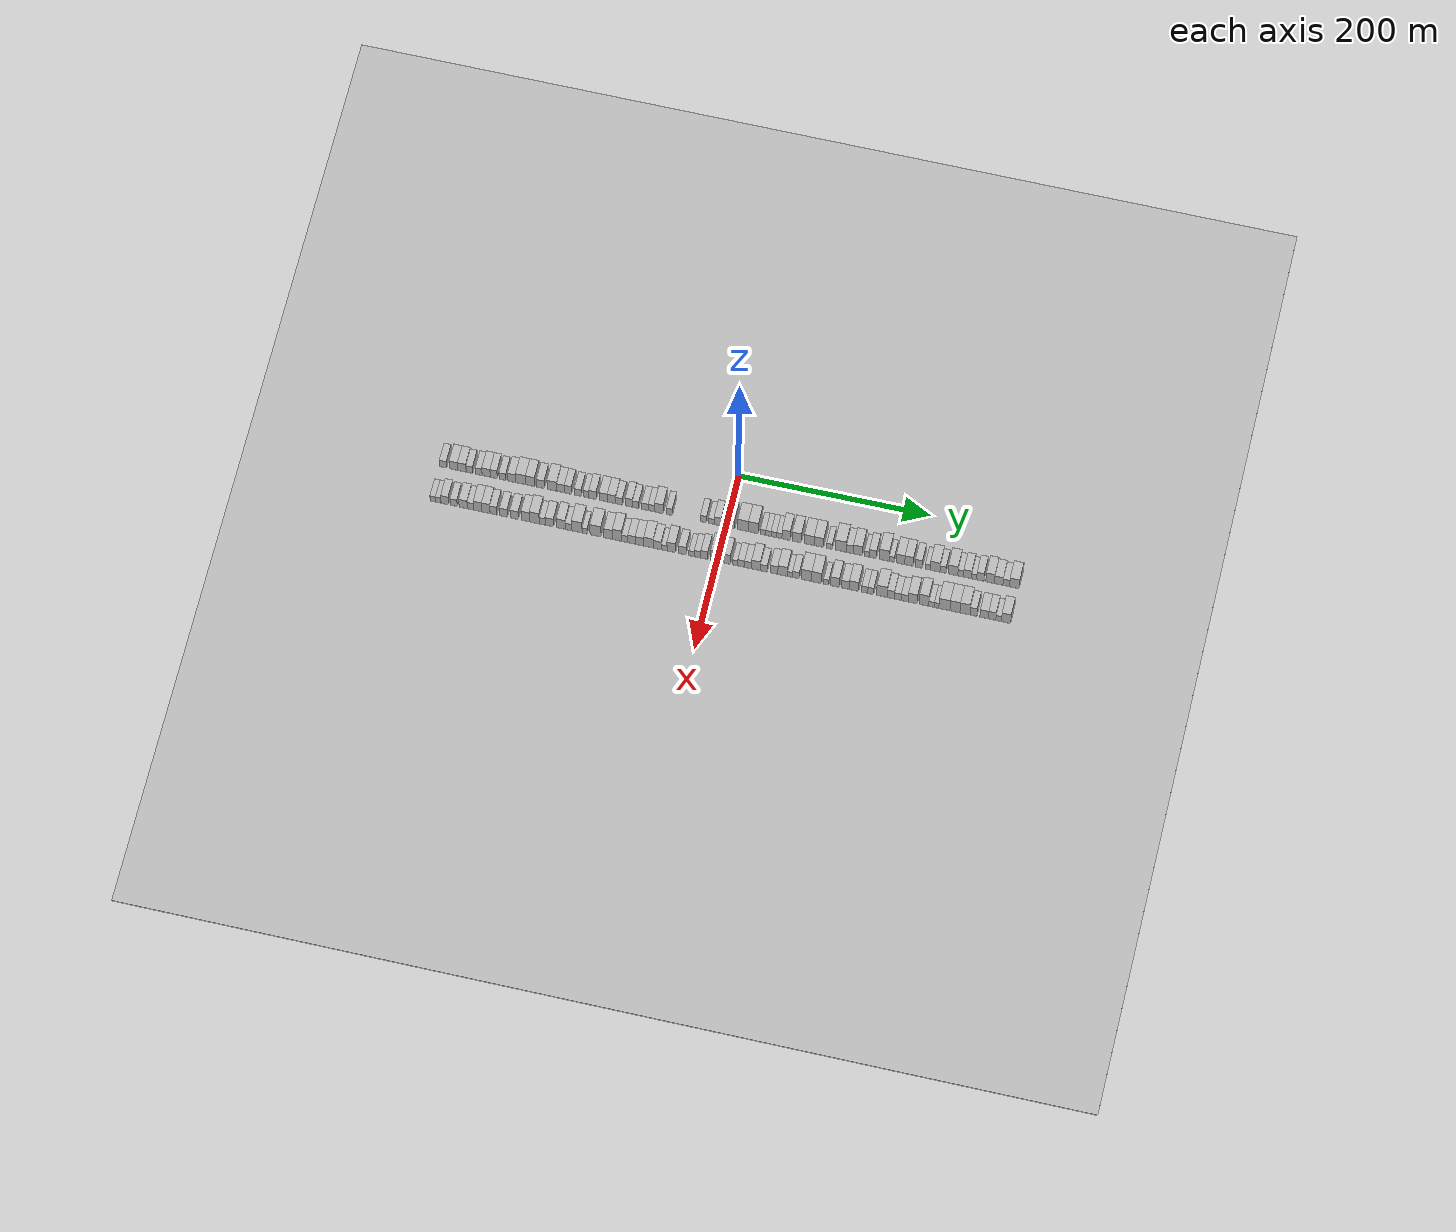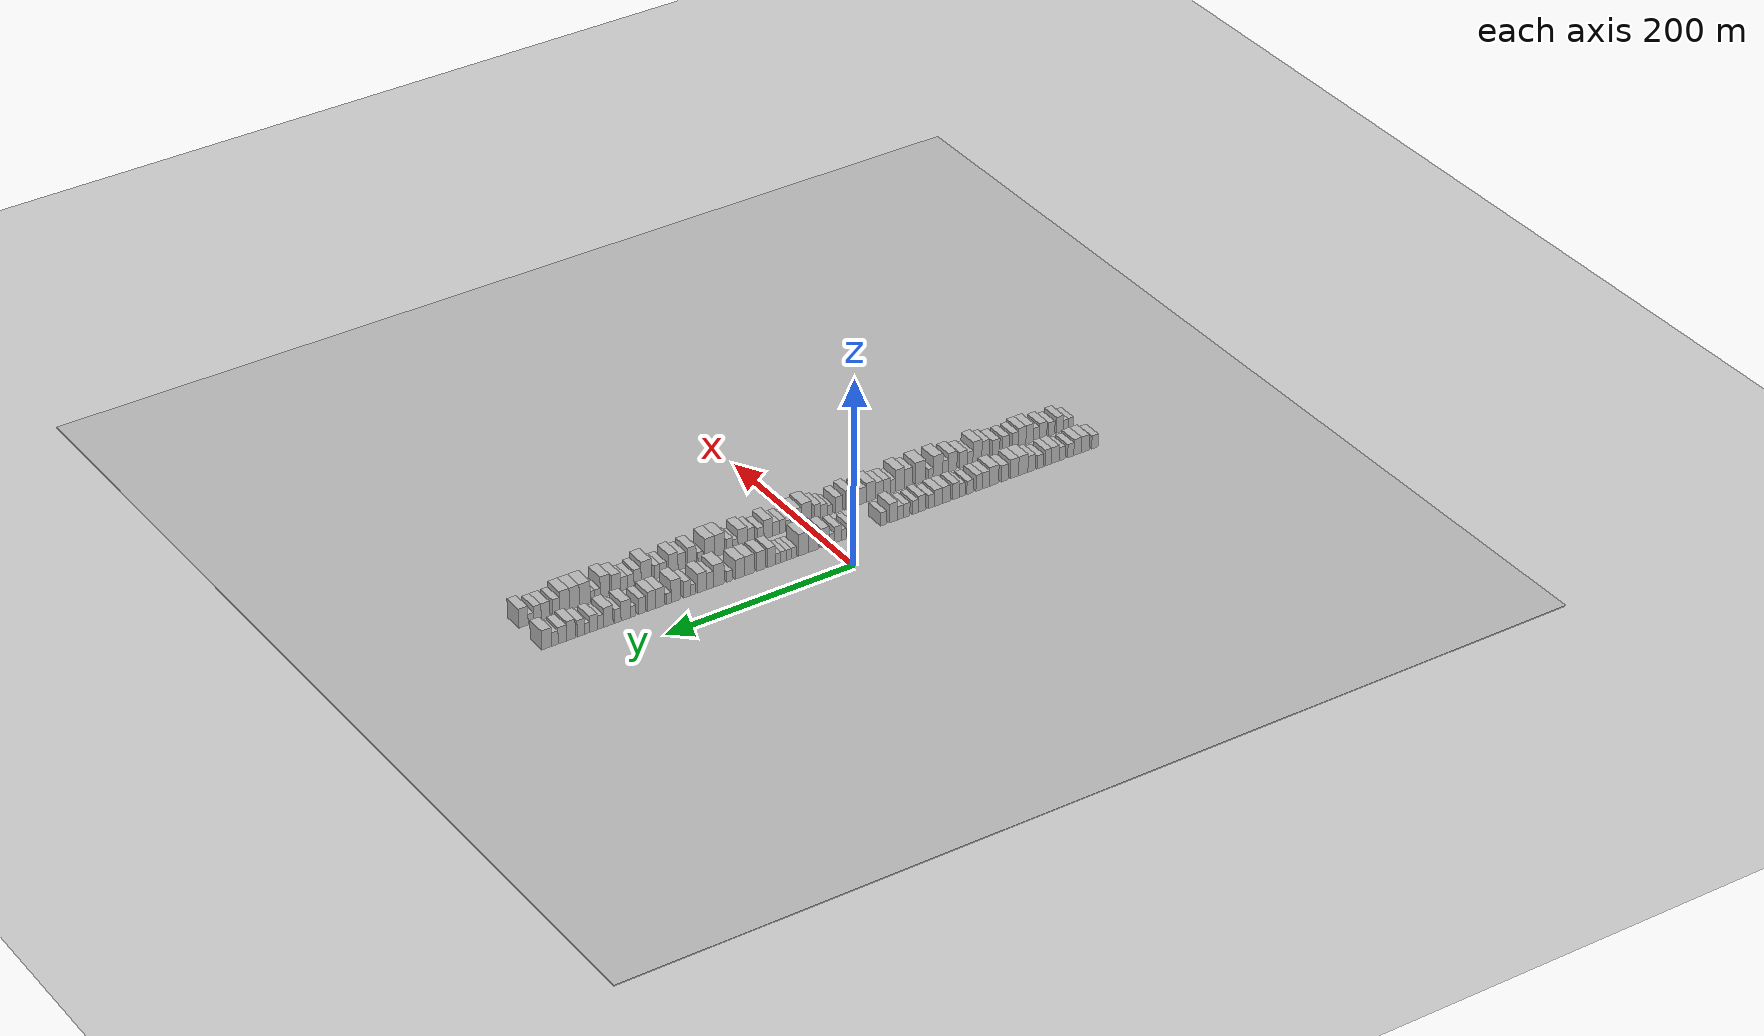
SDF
<?xml version="1.0" encoding="utf-8"?>

<sdf version="1.6">

   <world name="default">

      <gui fullscreen="0">

         <camera name="user_camera">

            <pose>-15 0 4.57585 0 0 0</pose>

            <view_controller>orbit</view_controller>

         </camera>

      </gui>

      <scene>

         <sky>

           <clouds>

             <speed>12</speed>

           </clouds>

         </sky>

         <ambient>0.4 0.4 0.4 1</ambient>

         <background>0.7 0.7 0.7 1</background>

         <shadows>1</shadows>

      </scene>

      <gravity>0 0 -9.8066</gravity>

      <magnetic_field>6e-06 2.3e-05 -4.2e-05</magnetic_field>

      <physics default="0" name="default_physics" type="ode">

         <ode>

            <solver>

               <type>quick</type>

               <iters>10</iters>

               <sor>1.0</sor>

               <use_dynamic_moi_rescaling>0</use_dynamic_moi_rescaling>

            </solver>

            <constraints>

               <cfm>0</cfm>

               <erp>0.2</erp>

               <contact_max_correcting_vel>100</contact_max_correcting_vel>

               <contact_surface_layer>0.001</contact_surface_layer>

            </constraints>

         </ode>

         <max_step_size>0.004</max_step_size>

         <real_time_factor>1</real_time_factor>

         <real_time_update_rate>250</real_time_update_rate>

      </physics>

      <light name="sun" type="directional">

         <cast_shadows>1</cast_shadows>

         <pose>0 0 10 0 0 0</pose>

         <diffuse>0.8 0.8 0.8 1</diffuse>

         <specular>0.2 0.2 0.2 1</specular>

         <attenuation>

            <range>1000</range>

            <constant>0.9</constant>

            <linear>0.01</linear>

            <quadratic>0.001</quadratic>

         </attenuation>

         <direction>-0.5 0.1 -0.9</direction>

      </light>

      <include>

         <name>ground_plane_1</name>

         <uri>model://HANNAS_ground_plane</uri>

         <pose>0 0 0  0 0 0</pose>

      </include>

      <include>

         <name>ground_plane_2</name>

         <uri>model://HANNAS_ground_plane</uri>

         <pose>100 0 0  0 0 0</pose>

      </include>

      <model name="building_1">

         <static>1</static>

         <pose frame="">50.0000 -296.3226 0 0.000000 0.000000 0.000000</pose>

         <link name="link">

            <pose frame="">0 0 7.50 0 0 0</pose>

            <collision name="collision">

               <geometry>

                  <box>

                     <size>20.0000 7.3548 15.0000</size>

                  </box>

               </geometry>

               <max_contacts>10</max_contacts>

               <surface>

                  <contact>

                     <ode/>

                  </contact>

                  <bounce/>

                  <friction>

                     <torsional>

                        <ode/>

                     </torsional>

                     <ode/>

                  </friction>

               </surface>

            </collision>

            <visual name="visual">

               <cast_shadows>0</cast_shadows>

               <geometry>

                  <box>

                     <size>20.0000 7.3548 15.0000</size>

                  </box>

               </geometry>

               <material>

                  <script>

                     <uri>model://HANNAS_wall/materials/scripts</uri>

                     <uri>model://HANNAS_wall/materials/textures</uri>

                     <name>vrc/HANNAS_wall</name>

                  </script>

               </material>

            </visual>

            <self_collide>0</self_collide>

            <enable_wind>0</enable_wind>

            <kinematic>0</kinematic>

         </link>

      </model>

      <model name="building_2">

         <static>1</static>

         <pose frame="">50.0000 -285.2588 0 0.000000 0.000000 0.000000</pose>

         <link name="link">

            <pose frame="">0 0 9.00 0 0 0</pose>

            <collision name="collision">

               <geometry>

                  <box>

                     <size>20.0000 8.7729 18.0000</size>

                  </box>

               </geometry>

               <max_contacts>10</max_contacts>

               <surface>

                  <contact>

                     <ode/>

                  </contact>

                  <bounce/>

                  <friction>

                     <torsional>

                        <ode/>

                     </torsional>

                     <ode/>

                  </friction>

               </surface>

            </collision>

            <visual name="visual">

               <cast_shadows>0</cast_shadows>

               <geometry>

                  <box>

                     <size>20.0000 8.7729 18.0000</size>

                  </box>

               </geometry>

               <material>

                  <script>

                     <uri>model://HANNAS_wall/materials/scripts</uri>

                     <uri>model://HANNAS_wall/materials/textures</uri>

                     <name>vrc/HANNAS_wall</name>

                  </script>

               </material>

            </visual>

            <self_collide>0</self_collide>

            <enable_wind>0</enable_wind>

            <kinematic>0</kinematic>

         </link>

      </model>

      <model name="building_3">

         <static>1</static>

         <pose frame="">50.0000 -276.5379 0 0.000000 0.000000 0.000000</pose>

         <link name="link">

            <pose frame="">0 0 9.00 0 0 0</pose>

            <collision name="collision">

               <geometry>

                  <box>

                     <size>20.0000 8.6689 18.0000</size>

                  </box>

               </geometry>

               <max_contacts>10</max_contacts>

               <surface>

                  <contact>

                     <ode/>

                  </contact>

                  <bounce/>

                  <friction>

                     <torsional>

                        <ode/>

                     </torsional>

                     <ode/>

                  </friction>

               </surface>

            </collision>

            <visual name="visual">

               <cast_shadows>0</cast_shadows>

               <geometry>

                  <box>

                     <size>20.0000 8.6689 18.0000</size>

                  </box>

               </geometry>

               <material>

                  <script>

                     <uri>model://HANNAS_wall/materials/scripts</uri>

                     <uri>model://HANNAS_wall/materials/textures</uri>

                     <name>vrc/HANNAS_wall</name>

                  </script>

               </material>

            </visual>

            <self_collide>0</self_collide>

            <enable_wind>0</enable_wind>

            <kinematic>0</kinematic>

         </link>

      </model>

      <model name="building_4">

         <static>1</static>

         <pose frame="">50.0000 -268.7203 0 0.000000 0.000000 0.000000</pose>

         <link name="link">

            <pose frame="">0 0 7.50 0 0 0</pose>

            <collision name="collision">

               <geometry>

                  <box>

                     <size>20.0000 6.9662 15.0000</size>

                  </box>

               </geometry>

               <max_contacts>10</max_contacts>

               <surface>

                  <contact>

                     <ode/>

                  </contact>

                  <bounce/>

                  <friction>

                     <torsional>

                        <ode/>

                     </torsional>

                     <ode/>

                  </friction>

               </surface>

            </collision>

            <visual name="visual">

               <cast_shadows>0</cast_shadows>

               <geometry>

                  <box>

                     <size>20.0000 6.9662 15.0000</size>

                  </box>

               </geometry>

               <material>

                  <script>

                     <uri>model://HANNAS_wall/materials/scripts</uri>

                     <uri>model://HANNAS_wall/materials/textures</uri>

                     <name>vrc/HANNAS_wall</name>

                  </script>

               </material>

            </visual>

            <self_collide>0</self_collide>

            <enable_wind>0</enable_wind>

            <kinematic>0</kinematic>

         </link>

      </model>

      <model name="building_5">

         <static>1</static>

         <pose frame="">50.0000 -258.8322 0 0.000000 0.000000 0.000000</pose>

         <link name="link">

            <pose frame="">0 0 7.50 0 0 0</pose>

            <collision name="collision">

               <geometry>

                  <box>

                     <size>20.0000 6.8100 15.0000</size>

                  </box>

               </geometry>

               <max_contacts>10</max_contacts>

               <surface>

                  <contact>

                     <ode/>

                  </contact>

                  <bounce/>

                  <friction>

                     <torsional>

                        <ode/>

                     </torsional>

                     <ode/>

                  </friction>

               </surface>

            </collision>

            <visual name="visual">

               <cast_shadows>0</cast_shadows>

               <geometry>

                  <box>

                     <size>20.0000 6.8100 15.0000</size>

                  </box>

               </geometry>

               <material>

                  <script>

                     <uri>model://HANNAS_wall/materials/scripts</uri>

                     <uri>model://HANNAS_wall/materials/textures</uri>

                     <name>vrc/HANNAS_wall</name>

                  </script>

               </material>

            </visual>

            <self_collide>0</self_collide>

            <enable_wind>0</enable_wind>

            <kinematic>0</kinematic>

         </link>

      </model>

      <model name="building_6">

         <static>1</static>

         <pose frame="">50.0000 -251.1433 0 0.000000 0.000000 0.000000</pose>

         <link name="link">

            <pose frame="">0 0 9.00 0 0 0</pose>

            <collision name="collision">

               <geometry>

                  <box>

                     <size>20.0000 8.5678 18.0000</size>

                  </box>

               </geometry>

               <max_contacts>10</max_contacts>

               <surface>

                  <contact>

                     <ode/>

                  </contact>

                  <bounce/>

                  <friction>

                     <torsional>

                        <ode/>

                     </torsional>

                     <ode/>

                  </friction>

               </surface>

            </collision>

            <visual name="visual">

               <cast_shadows>0</cast_shadows>

               <geometry>

                  <box>

                     <size>20.0000 8.5678 18.0000</size>

                  </box>

               </geometry>

               <material>

                  <script>

                     <uri>model://HANNAS_wall/materials/scripts</uri>

                     <uri>model://HANNAS_wall/materials/textures</uri>

                     <name>vrc/HANNAS_wall</name>

                  </script>

               </material>

            </visual>

            <self_collide>0</self_collide>

            <enable_wind>0</enable_wind>

            <kinematic>0</kinematic>

         </link>

      </model>

      <model name="building_7">

         <static>1</static>

         <pose frame="">50.0000 -243.2045 0 0.000000 0.000000 0.000000</pose>

         <link name="link">

            <pose frame="">0 0 9.00 0 0 0</pose>

            <collision name="collision">

               <geometry>

                  <box>

                     <size>20.0000 7.3098 18.0000</size>

                  </box>

               </geometry>

               <max_contacts>10</max_contacts>

               <surface>

                  <contact>

                     <ode/>

                  </contact>

                  <bounce/>

                  <friction>

                     <torsional>

                        <ode/>

                     </torsional>

                     <ode/>

                  </friction>

               </surface>

            </collision>

            <visual name="visual">

               <cast_shadows>0</cast_shadows>

               <geometry>

                  <box>

                     <size>20.0000 7.3098 18.0000</size>

                  </box>

               </geometry>

               <material>

                  <script>

                     <uri>model://HANNAS_wall/materials/scripts</uri>

                     <uri>model://HANNAS_wall/materials/textures</uri>

                     <name>vrc/HANNAS_wall</name>

                  </script>

               </material>

            </visual>

            <self_collide>0</self_collide>

            <enable_wind>0</enable_wind>

            <kinematic>0</kinematic>

         </link>

      </model>

      <model name="building_8">

         <static>1</static>

         <pose frame="">50.0000 -233.9707 0 0.000000 0.000000 0.000000</pose>

         <link name="link">

            <pose frame="">0 0 7.50 0 0 0</pose>

            <collision name="collision">

               <geometry>

                  <box>

                     <size>20.0000 7.1579 15.0000</size>

                  </box>

               </geometry>

               <max_contacts>10</max_contacts>

               <surface>

                  <contact>

                     <ode/>

                  </contact>

                  <bounce/>

                  <friction>

                     <torsional>

                        <ode/>

                     </torsional>

                     <ode/>

                  </friction>

               </surface>

            </collision>

            <visual name="visual">

               <cast_shadows>0</cast_shadows>

               <geometry>

                  <box>

                     <size>20.0000 7.1579 15.0000</size>

                  </box>

               </geometry>

               <material>

                  <script>

                     <uri>model://HANNAS_wall/materials/scripts</uri>

                     <uri>model://HANNAS_wall/materials/textures</uri>

                     <name>vrc/HANNAS_wall</name>

                  </script>

               </material>

            </visual>

            <self_collide>0</self_collide>

            <enable_wind>0</enable_wind>

            <kinematic>0</kinematic>

         </link>

      </model>

      <model name="building_9">

         <static>1</static>

         <pose frame="">50.0000 -224.2129 0 0.000000 0.000000 0.000000</pose>

         <link name="link">

            <pose frame="">0 0 9.00 0 0 0</pose>

            <collision name="collision">

               <geometry>

                  <box>

                     <size>20.0000 8.3578 18.0000</size>

                  </box>

               </geometry>

               <max_contacts>10</max_contacts>

               <surface>

                  <contact>

                     <ode/>

                  </contact>

                  <bounce/>

                  <friction>

                     <torsional>

                        <ode/>

                     </torsional>

                     <ode/>

                  </friction>

               </surface>

            </collision>

            <visual name="visual">

               <cast_shadows>0</cast_shadows>

               <geometry>

                  <box>

                     <size>20.0000 8.3578 18.0000</size>

                  </box>

               </geometry>

               <material>

                  <script>

                     <uri>model://HANNAS_wall/materials/scripts</uri>

                     <uri>model://HANNAS_wall/materials/textures</uri>

                     <name>vrc/HANNAS_wall</name>

                  </script>

               </material>

            </visual>

            <self_collide>0</self_collide>

            <enable_wind>0</enable_wind>

            <kinematic>0</kinematic>

         </link>

      </model>

      <model name="building_10">

         <static>1</static>

         <pose frame="">50.0000 -214.8225 0 0.000000 0.000000 0.000000</pose>

         <link name="link">

            <pose frame="">0 0 10.50 0 0 0</pose>

            <collision name="collision">

               <geometry>

                  <box>

                     <size>20.0000 10.4230 21.0000</size>

                  </box>

               </geometry>

               <max_contacts>10</max_contacts>

               <surface>

                  <contact>

                     <ode/>

                  </contact>

                  <bounce/>

                  <friction>

                     <torsional>

                        <ode/>

                     </torsional>

                     <ode/>

                  </friction>

               </surface>

            </collision>

            <visual name="visual">

               <cast_shadows>0</cast_shadows>

               <geometry>

                  <box>

                     <size>20.0000 10.4230 21.0000</size>

                  </box>

               </geometry>

               <material>

                  <script>

                     <uri>model://HANNAS_wall/materials/scripts</uri>

                     <uri>model://HANNAS_wall/materials/textures</uri>

                     <name>vrc/HANNAS_wall</name>

                  </script>

               </material>

            </visual>

            <self_collide>0</self_collide>

            <enable_wind>0</enable_wind>

            <kinematic>0</kinematic>

         </link>

      </model>

      <model name="building_11">

         <static>1</static>

         <pose frame="">50.0000 -204.8685 0 0.000000 0.000000 0.000000</pose>

         <link name="link">

            <pose frame="">0 0 10.50 0 0 0</pose>

            <collision name="collision">

               <geometry>

                  <box>

                     <size>20.0000 9.4849 21.0000</size>

                  </box>

               </geometry>

               <max_contacts>10</max_contacts>

               <surface>

                  <contact>

                     <ode/>

                  </contact>

                  <bounce/>

                  <friction>

                     <torsional>

                        <ode/>

                     </torsional>

                     <ode/>

                  </friction>

               </surface>

            </collision>

            <visual name="visual">

               <cast_shadows>0</cast_shadows>

               <geometry>

                  <box>

                     <size>20.0000 9.4849 21.0000</size>

                  </box>

               </geometry>

               <material>

                  <script>

                     <uri>model://HANNAS_wall/materials/scripts</uri>

                     <uri>model://HANNAS_wall/materials/textures</uri>

                     <name>vrc/HANNAS_wall</name>

                  </script>

               </material>

            </visual>

            <self_collide>0</self_collide>

            <enable_wind>0</enable_wind>

            <kinematic>0</kinematic>

         </link>

      </model>

      <model name="building_12">

         <static>1</static>

         <pose frame="">50.0000 -194.1113 0 0.000000 0.000000 0.000000</pose>

         <link name="link">

            <pose frame="">0 0 9.00 0 0 0</pose>

            <collision name="collision">

               <geometry>

                  <box>

                     <size>20.0000 8.0295 18.0000</size>

                  </box>

               </geometry>

               <max_contacts>10</max_contacts>

               <surface>

                  <contact>

                     <ode/>

                  </contact>

                  <bounce/>

                  <friction>

                     <torsional>

                        <ode/>

                     </torsional>

                     <ode/>

                  </friction>

               </surface>

            </collision>

            <visual name="visual">

               <cast_shadows>0</cast_shadows>

               <geometry>

                  <box>

                     <size>20.0000 8.0295 18.0000</size>

                  </box>

               </geometry>

               <material>

                  <script>

                     <uri>model://HANNAS_wall/materials/scripts</uri>

                     <uri>model://HANNAS_wall/materials/textures</uri>

                     <name>vrc/HANNAS_wall</name>

                  </script>

               </material>

            </visual>

            <self_collide>0</self_collide>

            <enable_wind>0</enable_wind>

            <kinematic>0</kinematic>

         </link>

      </model>

      <model name="building_13">

         <static>1</static>

         <pose frame="">50.0000 -181.9876 0 0.000000 0.000000 0.000000</pose>

         <link name="link">

            <pose frame="">0 0 10.50 0 0 0</pose>

            <collision name="collision">

               <geometry>

                  <box>

                     <size>20.0000 10.2180 21.0000</size>

                  </box>

               </geometry>

               <max_contacts>10</max_contacts>

               <surface>

                  <contact>

                     <ode/>

                  </contact>

                  <bounce/>

                  <friction>

                     <torsional>

                        <ode/>

                     </torsional>

                     <ode/>

                  </friction>

               </surface>

            </collision>

            <visual name="visual">

               <cast_shadows>0</cast_shadows>

               <geometry>

                  <box>

                     <size>20.0000 10.2180 21.0000</size>

                  </box>

               </geometry>

               <material>

                  <script>

                     <uri>model://HANNAS_wall/materials/scripts</uri>

                     <uri>model://HANNAS_wall/materials/textures</uri>

                     <name>vrc/HANNAS_wall</name>

                  </script>

               </material>

            </visual>

            <self_collide>0</self_collide>

            <enable_wind>0</enable_wind>

            <kinematic>0</kinematic>

         </link>

      </model>

      <model name="building_14">

         <static>1</static>

         <pose frame="">50.0000 -172.9549 0 0.000000 0.000000 0.000000</pose>

         <link name="link">

            <pose frame="">0 0 9.00 0 0 0</pose>

            <collision name="collision">

               <geometry>

                  <box>

                     <size>20.0000 7.8474 18.0000</size>

                  </box>

               </geometry>

               <max_contacts>10</max_contacts>

               <surface>

                  <contact>

                     <ode/>

                  </contact>

                  <bounce/>

                  <friction>

                     <torsional>

                        <ode/>

                     </torsional>

                     <ode/>

                  </friction>

               </surface>

            </collision>

            <visual name="visual">

               <cast_shadows>0</cast_shadows>

               <geometry>

                  <box>

                     <size>20.0000 7.8474 18.0000</size>

                  </box>

               </geometry>

               <material>

                  <script>

                     <uri>model://HANNAS_wall/materials/scripts</uri>

                     <uri>model://HANNAS_wall/materials/textures</uri>

                     <name>vrc/HANNAS_wall</name>

                  </script>

               </material>

            </visual>

            <self_collide>0</self_collide>

            <enable_wind>0</enable_wind>

            <kinematic>0</kinematic>

         </link>

      </model>

      <model name="building_15">

         <static>1</static>

         <pose frame="">50.0000 -165.3196 0 0.000000 0.000000 0.000000</pose>

         <link name="link">

            <pose frame="">0 0 9.00 0 0 0</pose>

            <collision name="collision">

               <geometry>

                  <box>

                     <size>20.0000 7.4234 18.0000</size>

                  </box>

               </geometry>

               <max_contacts>10</max_contacts>

               <surface>

                  <contact>

                     <ode/>

                  </contact>

                  <bounce/>

                  <friction>

                     <torsional>

                        <ode/>

                     </torsional>

                     <ode/>

                  </friction>

               </surface>

            </collision>

            <visual name="visual">

               <cast_shadows>0</cast_shadows>

               <geometry>

                  <box>

                     <size>20.0000 7.4234 18.0000</size>

                  </box>

               </geometry>

               <material>

                  <script>

                     <uri>model://HANNAS_wall/materials/scripts</uri>

                     <uri>model://HANNAS_wall/materials/textures</uri>

                     <name>vrc/HANNAS_wall</name>

                  </script>

               </material>

            </visual>

            <self_collide>0</self_collide>

            <enable_wind>0</enable_wind>

            <kinematic>0</kinematic>

         </link>

      </model>

      <model name="building_16">

         <static>1</static>

         <pose frame="">50.0000 -155.0057 0 0.000000 0.000000 0.000000</pose>

         <link name="link">

            <pose frame="">0 0 7.50 0 0 0</pose>

            <collision name="collision">

               <geometry>

                  <box>

                     <size>20.0000 7.2043 15.0000</size>

                  </box>

               </geometry>

               <max_contacts>10</max_contacts>

               <surface>

                  <contact>

                     <ode/>

                  </contact>

                  <bounce/>

                  <friction>

                     <torsional>

                        <ode/>

                     </torsional>

                     <ode/>

                  </friction>

               </surface>

            </collision>

            <visual name="visual">

               <cast_shadows>0</cast_shadows>

               <geometry>

                  <box>

                     <size>20.0000 7.2043 15.0000</size>

                  </box>

               </geometry>

               <material>

                  <script>

                     <uri>model://HANNAS_wall/materials/scripts</uri>

                     <uri>model://HANNAS_wall/materials/textures</uri>

                     <name>vrc/HANNAS_wall</name>

                  </script>

               </material>

            </visual>

            <self_collide>0</self_collide>

            <enable_wind>0</enable_wind>

            <kinematic>0</kinematic>

         </link>

      </model>

      <model name="building_17">

         <static>1</static>

         <pose frame="">50.0000 -146.3915 0 0.000000 0.000000 0.000000</pose>

         <link name="link">

            <pose frame="">0 0 7.50 0 0 0</pose>

            <collision name="collision">

               <geometry>

                  <box>

                     <size>20.0000 6.0242 15.0000</size>

                  </box>

               </geometry>

               <max_contacts>10</max_contacts>

               <surface>

                  <contact>

                     <ode/>

                  </contact>

                  <bounce/>

                  <friction>

                     <torsional>

                        <ode/>

                     </torsional>

                     <ode/>

                  </friction>

               </surface>

            </collision>

            <visual name="visual">

               <cast_shadows>0</cast_shadows>

               <geometry>

                  <box>

                     <size>20.0000 6.0242 15.0000</size>

                  </box>

               </geometry>

               <material>

                  <script>

                     <uri>model://HANNAS_wall/materials/scripts</uri>

                     <uri>model://HANNAS_wall/materials/textures</uri>

                     <name>vrc/HANNAS_wall</name>

                  </script>

               </material>

            </visual>

            <self_collide>0</self_collide>

            <enable_wind>0</enable_wind>

            <kinematic>0</kinematic>

         </link>

      </model>

      <model name="building_18">

         <static>1</static>

         <pose frame="">50.0000 -139.5196 0 0.000000 0.000000 0.000000</pose>

         <link name="link">

            <pose frame="">0 0 9.00 0 0 0</pose>

            <collision name="collision">

               <geometry>

                  <box>

                     <size>20.0000 7.7195 18.0000</size>

                  </box>

               </geometry>

               <max_contacts>10</max_contacts>

               <surface>

                  <contact>

                     <ode/>

                  </contact>

                  <bounce/>

                  <friction>

                     <torsional>

                        <ode/>

                     </torsional>

                     <ode/>

                  </friction>

               </surface>

            </collision>

            <visual name="visual">

               <cast_shadows>0</cast_shadows>

               <geometry>

                  <box>

                     <size>20.0000 7.7195 18.0000</size>

                  </box>

               </geometry>

               <material>

                  <script>

                     <uri>model://HANNAS_wall/materials/scripts</uri>

                     <uri>model://HANNAS_wall/materials/textures</uri>

                     <name>vrc/HANNAS_wall</name>

                  </script>

               </material>

            </visual>

            <self_collide>0</self_collide>

            <enable_wind>0</enable_wind>

            <kinematic>0</kinematic>

         </link>

      </model>

      <model name="building_19">

         <static>1</static>

         <pose frame="">50.0000 -128.3467 0 0.000000 0.000000 0.000000</pose>

         <link name="link">

            <pose frame="">0 0 9.00 0 0 0</pose>

            <collision name="collision">

               <geometry>

                  <box>

                     <size>20.0000 8.6264 18.0000</size>

                  </box>

               </geometry>

               <max_contacts>10</max_contacts>

               <surface>

                  <contact>

                     <ode/>

                  </contact>

                  <bounce/>

                  <friction>

                     <torsional>

                        <ode/>

                     </torsional>

                     <ode/>

                  </friction>

               </surface>

            </collision>

            <visual name="visual">

               <cast_shadows>0</cast_shadows>

               <geometry>

                  <box>

                     <size>20.0000 8.6264 18.0000</size>

                  </box>

               </geometry>

               <material>

                  <script>

                     <uri>model://HANNAS_wall/materials/scripts</uri>

                     <uri>model://HANNAS_wall/materials/textures</uri>

                     <name>vrc/HANNAS_wall</name>

                  </script>

               </material>

            </visual>

            <self_collide>0</self_collide>

            <enable_wind>0</enable_wind>

            <kinematic>0</kinematic>

         </link>

      </model>

      <model name="building_20">

         <static>1</static>

         <pose frame="">50.0000 -119.6518 0 0.000000 0.000000 0.000000</pose>

         <link name="link">

            <pose frame="">0 0 9.00 0 0 0</pose>

            <collision name="collision">

               <geometry>

                  <box>

                     <size>20.0000 8.7634 18.0000</size>

                  </box>

               </geometry>

               <max_contacts>10</max_contacts>

               <surface>

                  <contact>

                     <ode/>

                  </contact>

                  <bounce/>

                  <friction>

                     <torsional>

                        <ode/>

                     </torsional>

                     <ode/>

                  </friction>

               </surface>

            </collision>

            <visual name="visual">

               <cast_shadows>0</cast_shadows>

               <geometry>

                  <box>

                     <size>20.0000 8.7634 18.0000</size>

                  </box>

               </geometry>

               <material>

                  <script>

                     <uri>model://HANNAS_wall/materials/scripts</uri>

                     <uri>model://HANNAS_wall/materials/textures</uri>

                     <name>vrc/HANNAS_wall</name>

                  </script>

               </material>

            </visual>

            <self_collide>0</self_collide>

            <enable_wind>0</enable_wind>

            <kinematic>0</kinematic>

         </link>

      </model>

      <model name="building_21">

         <static>1</static>

         <pose frame="">50.0000 -111.7621 0 0.000000 0.000000 0.000000</pose>

         <link name="link">

            <pose frame="">0 0 7.50 0 0 0</pose>

            <collision name="collision">

               <geometry>

                  <box>

                     <size>20.0000 7.0159 15.0000</size>

                  </box>

               </geometry>

               <max_contacts>10</max_contacts>

               <surface>

                  <contact>

                     <ode/>

                  </contact>

                  <bounce/>

                  <friction>

                     <torsional>

                        <ode/>

                     </torsional>

                     <ode/>

                  </friction>

               </surface>

            </collision>

            <visual name="visual">

               <cast_shadows>0</cast_shadows>

               <geometry>

                  <box>

                     <size>20.0000 7.0159 15.0000</size>

                  </box>

               </geometry>

               <material>

                  <script>

                     <uri>model://HANNAS_wall/materials/scripts</uri>

                     <uri>model://HANNAS_wall/materials/textures</uri>

                     <name>vrc/HANNAS_wall</name>

                  </script>

               </material>

            </visual>

            <self_collide>0</self_collide>

            <enable_wind>0</enable_wind>

            <kinematic>0</kinematic>

         </link>

      </model>

      <model name="building_22">

         <static>1</static>

         <pose frame="">50.0000 -101.4349 0 0.000000 0.000000 0.000000</pose>

         <link name="link">

            <pose frame="">0 0 9.00 0 0 0</pose>

            <collision name="collision">

               <geometry>

                  <box>

                     <size>20.0000 7.6385 18.0000</size>

                  </box>

               </geometry>

               <max_contacts>10</max_contacts>

               <surface>

                  <contact>

                     <ode/>

                  </contact>

                  <bounce/>

                  <friction>

                     <torsional>

                        <ode/>

                     </torsional>

                     <ode/>

                  </friction>

               </surface>

            </collision>

            <visual name="visual">

               <cast_shadows>0</cast_shadows>

               <geometry>

                  <box>

                     <size>20.0000 7.6385 18.0000</size>

                  </box>

               </geometry>

               <material>

                  <script>

                     <uri>model://HANNAS_wall/materials/scripts</uri>

                     <uri>model://HANNAS_wall/materials/textures</uri>

                     <name>vrc/HANNAS_wall</name>

                  </script>

               </material>

            </visual>

            <self_collide>0</self_collide>

            <enable_wind>0</enable_wind>

            <kinematic>0</kinematic>

         </link>

      </model>

      <model name="building_23">

         <static>1</static>

         <pose frame="">50.0000 -94.3597 0 0.000000 0.000000 0.000000</pose>

         <link name="link">

            <pose frame="">0 0 7.50 0 0 0</pose>

            <collision name="collision">

               <geometry>

                  <box>

                     <size>20.0000 6.5120 15.0000</size>

                  </box>

               </geometry>

               <max_contacts>10</max_contacts>

               <surface>

                  <contact>

                     <ode/>

                  </contact>

                  <bounce/>

                  <friction>

                     <torsional>

                        <ode/>

                     </torsional>

                     <ode/>

                  </friction>

               </surface>

            </collision>

            <visual name="visual">

               <cast_shadows>0</cast_shadows>

               <geometry>

                  <box>

                     <size>20.0000 6.5120 15.0000</size>

                  </box>

               </geometry>

               <material>

                  <script>

                     <uri>model://HANNAS_wall/materials/scripts</uri>

                     <uri>model://HANNAS_wall/materials/textures</uri>

                     <name>vrc/HANNAS_wall</name>

                  </script>

               </material>

            </visual>

            <self_collide>0</self_collide>

            <enable_wind>0</enable_wind>

            <kinematic>0</kinematic>

         </link>

      </model>

      <model name="building_24">

         <static>1</static>

         <pose frame="">50.0000 -84.7293 0 0.000000 0.000000 0.000000</pose>

         <link name="link">

            <pose frame="">0 0 7.50 0 0 0</pose>

            <collision name="collision">

               <geometry>

                  <box>

                     <size>20.0000 6.7488 15.0000</size>

                  </box>

               </geometry>

               <max_contacts>10</max_contacts>

               <surface>

                  <contact>

                     <ode/>

                  </contact>

                  <bounce/>

                  <friction>

                     <torsional>

                        <ode/>

                     </torsional>

                     <ode/>

                  </friction>

               </surface>

            </collision>

            <visual name="visual">

               <cast_shadows>0</cast_shadows>

               <geometry>

                  <box>

                     <size>20.0000 6.7488 15.0000</size>

                  </box>

               </geometry>

               <material>

                  <script>

                     <uri>model://HANNAS_wall/materials/scripts</uri>

                     <uri>model://HANNAS_wall/materials/textures</uri>

                     <name>vrc/HANNAS_wall</name>

                  </script>

               </material>

            </visual>

            <self_collide>0</self_collide>

            <enable_wind>0</enable_wind>

            <kinematic>0</kinematic>

         </link>

      </model>

      <model name="building_25">

         <static>1</static>

         <pose frame="">50.0000 -78.0399 0 0.000000 0.000000 0.000000</pose>

         <link name="link">

            <pose frame="">0 0 7.50 0 0 0</pose>

            <collision name="collision">

               <geometry>

                  <box>

                     <size>20.0000 6.6301 15.0000</size>

                  </box>

               </geometry>

               <max_contacts>10</max_contacts>

               <surface>

                  <contact>

                     <ode/>

                  </contact>

                  <bounce/>

                  <friction>

                     <torsional>

                        <ode/>

                     </torsional>

                     <ode/>

                  </friction>

               </surface>

            </collision>

            <visual name="visual">

               <cast_shadows>0</cast_shadows>

               <geometry>

                  <box>

                     <size>20.0000 6.6301 15.0000</size>

                  </box>

               </geometry>

               <material>

                  <script>

                     <uri>model://HANNAS_wall/materials/scripts</uri>

                     <uri>model://HANNAS_wall/materials/textures</uri>

                     <name>vrc/HANNAS_wall</name>

                  </script>

               </material>

            </visual>

            <self_collide>0</self_collide>

            <enable_wind>0</enable_wind>

            <kinematic>0</kinematic>

         </link>

      </model>

      <model name="building_26">

         <static>1</static>

         <pose frame="">50.0000 -70.1083 0 0.000000 0.000000 0.000000</pose>

         <link name="link">

            <pose frame="">0 0 10.50 0 0 0</pose>

            <collision name="collision">

               <geometry>

                  <box>

                     <size>20.0000 9.2331 21.0000</size>

                  </box>

               </geometry>

               <max_contacts>10</max_contacts>

               <surface>

                  <contact>

                     <ode/>

                  </contact>

                  <bounce/>

                  <friction>

                     <torsional>

                        <ode/>

                     </torsional>

                     <ode/>

                  </friction>

               </surface>

            </collision>

            <visual name="visual">

               <cast_shadows>0</cast_shadows>

               <geometry>

                  <box>

                     <size>20.0000 9.2331 21.0000</size>

                  </box>

               </geometry>

               <material>

                  <script>

                     <uri>model://HANNAS_wall/materials/scripts</uri>

                     <uri>model://HANNAS_wall/materials/textures</uri>

                     <name>vrc/HANNAS_wall</name>

                  </script>

               </material>

            </visual>

            <self_collide>0</self_collide>

            <enable_wind>0</enable_wind>

            <kinematic>0</kinematic>

         </link>

      </model>

      <model name="building_27">

         <static>1</static>

         <pose frame="">50.0000 -59.2978 0 0.000000 0.000000 0.000000</pose>

         <link name="link">

            <pose frame="">0 0 7.50 0 0 0</pose>

            <collision name="collision">

               <geometry>

                  <box>

                     <size>20.0000 6.3880 15.0000</size>

                  </box>

               </geometry>

               <max_contacts>10</max_contacts>

               <surface>

                  <contact>

                     <ode/>

                  </contact>

                  <bounce/>

                  <friction>

                     <torsional>

                        <ode/>

                     </torsional>

                     <ode/>

                  </friction>

               </surface>

            </collision>

            <visual name="visual">

               <cast_shadows>0</cast_shadows>

               <geometry>

                  <box>

                     <size>20.0000 6.3880 15.0000</size>

                  </box>

               </geometry>

               <material>

                  <script>

                     <uri>model://HANNAS_wall/materials/scripts</uri>

                     <uri>model://HANNAS_wall/materials/textures</uri>

                     <name>vrc/HANNAS_wall</name>

                  </script>

               </material>

            </visual>

            <self_collide>0</self_collide>

            <enable_wind>0</enable_wind>

            <kinematic>0</kinematic>

         </link>

      </model>

      <model name="building_28">

         <static>1</static>

         <pose frame="">50.0000 -23.5410 0 0.000000 0.000000 0.000000</pose>

         <link name="link">

            <pose frame="">0 0 7.50 0 0 0</pose>

            <collision name="collision">

               <geometry>

                  <box>

                     <size>20.0000 6.3752 15.0000</size>

                  </box>

               </geometry>

               <max_contacts>10</max_contacts>

               <surface>

                  <contact>

                     <ode/>

                  </contact>

                  <bounce/>

                  <friction>

                     <torsional>

                        <ode/>

                     </torsional>

                     <ode/>

                  </friction>

               </surface>

            </collision>

            <visual name="visual">

               <cast_shadows>0</cast_shadows>

               <geometry>

                  <box>

                     <size>20.0000 6.3752 15.0000</size>

                  </box>

               </geometry>

               <material>

                  <script>

                     <uri>model://HANNAS_wall/materials/scripts</uri>

                     <uri>model://HANNAS_wall/materials/textures</uri>

                     <name>vrc/HANNAS_wall</name>

                  </script>

               </material>

            </visual>

            <self_collide>0</self_collide>

            <enable_wind>0</enable_wind>

            <kinematic>0</kinematic>

         </link>

      </model>

      <model name="building_29">

         <static>1</static>

         <pose frame="">50.0000 -15.4080 0 0.000000 0.000000 0.000000</pose>

         <link name="link">

            <pose frame="">0 0 6.00 0 0 0</pose>

            <collision name="collision">

               <geometry>

                  <box>

                     <size>20.0000 5.8906 12.0000</size>

                  </box>

               </geometry>

               <max_contacts>10</max_contacts>

               <surface>

                  <contact>

                     <ode/>

                  </contact>

                  <bounce/>

                  <friction>

                     <torsional>

                        <ode/>

                     </torsional>

                     <ode/>

                  </friction>

               </surface>

            </collision>

            <visual name="visual">

               <cast_shadows>0</cast_shadows>

               <geometry>

                  <box>

                     <size>20.0000 5.8906 12.0000</size>

                  </box>

               </geometry>

               <material>

                  <script>

                     <uri>model://HANNAS_wall/materials/scripts</uri>

                     <uri>model://HANNAS_wall/materials/textures</uri>

                     <name>vrc/HANNAS_wall</name>

                  </script>

               </material>

            </visual>

            <self_collide>0</self_collide>

            <enable_wind>0</enable_wind>

            <kinematic>0</kinematic>

         </link>

      </model>

      <model name="building_30">

         <static>1</static>

         <pose frame="">50.0000 -8.6986 0 0.000000 0.000000 0.000000</pose>

         <link name="link">

            <pose frame="">0 0 9.00 0 0 0</pose>

            <collision name="collision">

               <geometry>

                  <box>

                     <size>20.0000 7.5284 18.0000</size>

                  </box>

               </geometry>

               <max_contacts>10</max_contacts>

               <surface>

                  <contact>

                     <ode/>

                  </contact>

                  <bounce/>

                  <friction>

                     <torsional>

                        <ode/>

                     </torsional>

                     <ode/>

                  </friction>

               </surface>

            </collision>

            <visual name="visual">

               <cast_shadows>0</cast_shadows>

               <geometry>

                  <box>

                     <size>20.0000 7.5284 18.0000</size>

                  </box>

               </geometry>

               <material>

                  <script>

                     <uri>model://HANNAS_wall/materials/scripts</uri>

                     <uri>model://HANNAS_wall/materials/textures</uri>

                     <name>vrc/HANNAS_wall</name>

                  </script>

               </material>

            </visual>

            <self_collide>0</self_collide>

            <enable_wind>0</enable_wind>

            <kinematic>0</kinematic>

         </link>

      </model>

      <model name="building_31">

         <static>1</static>

         <pose frame="">50.0000 -2.3356 0 0.000000 0.000000 0.000000</pose>

         <link name="link">

            <pose frame="">0 0 6.00 0 0 0</pose>

            <collision name="collision">

               <geometry>

                  <box>

                     <size>20.0000 5.1975 12.0000</size>

                  </box>

               </geometry>

               <max_contacts>10</max_contacts>

               <surface>

                  <contact>

                     <ode/>

                  </contact>

                  <bounce/>

                  <friction>

                     <torsional>

                        <ode/>

                     </torsional>

                     <ode/>

                  </friction>

               </surface>

            </collision>

            <visual name="visual">

               <cast_shadows>0</cast_shadows>

               <geometry>

                  <box>

                     <size>20.0000 5.1975 12.0000</size>

                  </box>

               </geometry>

               <material>

                  <script>

                     <uri>model://HANNAS_wall/materials/scripts</uri>

                     <uri>model://HANNAS_wall/materials/textures</uri>

                     <name>vrc/HANNAS_wall</name>

                  </script>

               </material>

            </visual>

            <self_collide>0</self_collide>

            <enable_wind>0</enable_wind>

            <kinematic>0</kinematic>

         </link>

      </model>

      <model name="building_32">

         <static>1</static>

         <pose frame="">50.0000 4.6970 0 0.000000 0.000000 0.000000</pose>

         <link name="link">

            <pose frame="">0 0 10.50 0 0 0</pose>

            <collision name="collision">

               <geometry>

                  <box>

                     <size>20.0000 8.8677 21.0000</size>

                  </box>

               </geometry>

               <max_contacts>10</max_contacts>

               <surface>

                  <contact>

                     <ode/>

                  </contact>

                  <bounce/>

                  <friction>

                     <torsional>

                        <ode/>

                     </torsional>

                     <ode/>

                  </friction>

               </surface>

            </collision>

            <visual name="visual">

               <cast_shadows>0</cast_shadows>

               <geometry>

                  <box>

                     <size>20.0000 8.8677 21.0000</size>

                  </box>

               </geometry>

               <material>

                  <script>

                     <uri>model://HANNAS_wall/materials/scripts</uri>

                     <uri>model://HANNAS_wall/materials/textures</uri>

                     <name>vrc/HANNAS_wall</name>

                  </script>

               </material>

            </visual>

            <self_collide>0</self_collide>

            <enable_wind>0</enable_wind>

            <kinematic>0</kinematic>

         </link>

      </model>

      <model name="building_33">

         <static>1</static>

         <pose frame="">50.0000 17.7263 0 0.000000 0.000000 0.000000</pose>

         <link name="link">

            <pose frame="">0 0 12.00 0 0 0</pose>

            <collision name="collision">

               <geometry>

                  <box>

                     <size>20.0000 11.1909 24.0000</size>

                  </box>

               </geometry>

               <max_contacts>10</max_contacts>

               <surface>

                  <contact>

                     <ode/>

                  </contact>

                  <bounce/>

                  <friction>

                     <torsional>

                        <ode/>

                     </torsional>

                     <ode/>

                  </friction>

               </surface>

            </collision>

            <visual name="visual">

               <cast_shadows>0</cast_shadows>

               <geometry>

                  <box>

                     <size>20.0000 11.1909 24.0000</size>

                  </box>

               </geometry>

               <material>

                  <script>

                     <uri>model://HANNAS_wall/materials/scripts</uri>

                     <uri>model://HANNAS_wall/materials/textures</uri>

                     <name>vrc/HANNAS_wall</name>

                  </script>

               </material>

            </visual>

            <self_collide>0</self_collide>

            <enable_wind>0</enable_wind>

            <kinematic>0</kinematic>

         </link>

      </model>

      <model name="building_34">

         <static>1</static>

         <pose frame="">50.0000 28.5475 0 0.000000 0.000000 0.000000</pose>

         <link name="link">

            <pose frame="">0 0 12.00 0 0 0</pose>

            <collision name="collision">

               <geometry>

                  <box>

                     <size>20.0000 10.4515 24.0000</size>

                  </box>

               </geometry>

               <max_contacts>10</max_contacts>

               <surface>

                  <contact>

                     <ode/>

                  </contact>

                  <bounce/>

                  <friction>

                     <torsional>

                        <ode/>

                     </torsional>

                     <ode/>

                  </friction>

               </surface>

            </collision>

            <visual name="visual">

               <cast_shadows>0</cast_shadows>

               <geometry>

                  <box>

                     <size>20.0000 10.4515 24.0000</size>

                  </box>

               </geometry>

               <material>

                  <script>

                     <uri>model://HANNAS_wall/materials/scripts</uri>

                     <uri>model://HANNAS_wall/materials/textures</uri>

                     <name>vrc/HANNAS_wall</name>

                  </script>

               </material>

            </visual>

            <self_collide>0</self_collide>

            <enable_wind>0</enable_wind>

            <kinematic>0</kinematic>

         </link>

      </model>

      <model name="building_35">

         <static>1</static>

         <pose frame="">50.0000 38.5941 0 0.000000 0.000000 0.000000</pose>

         <link name="link">

            <pose frame="">0 0 6.00 0 0 0</pose>

            <collision name="collision">

               <geometry>

                  <box>

                     <size>20.0000 5.6416 12.0000</size>

                  </box>

               </geometry>

               <max_contacts>10</max_contacts>

               <surface>

                  <contact>

                     <ode/>

                  </contact>

                  <bounce/>

                  <friction>

                     <torsional>

                        <ode/>

                     </torsional>

                     <ode/>

                  </friction>

               </surface>

            </collision>

            <visual name="visual">

               <cast_shadows>0</cast_shadows>

               <geometry>

                  <box>

                     <size>20.0000 5.6416 12.0000</size>

                  </box>

               </geometry>

               <material>

                  <script>

                     <uri>model://HANNAS_wall/materials/scripts</uri>

                     <uri>model://HANNAS_wall/materials/textures</uri>

                     <name>vrc/HANNAS_wall</name>

                  </script>

               </material>

            </visual>

            <self_collide>0</self_collide>

            <enable_wind>0</enable_wind>

            <kinematic>0</kinematic>

         </link>

      </model>

      <model name="building_36">

         <static>1</static>

         <pose frame="">50.0000 44.1248 0 0.000000 0.000000 0.000000</pose>

         <link name="link">

            <pose frame="">0 0 6.00 0 0 0</pose>

            <collision name="collision">

               <geometry>

                  <box>

                     <size>20.0000 5.4198 12.0000</size>

                  </box>

               </geometry>

               <max_contacts>10</max_contacts>

               <surface>

                  <contact>

                     <ode/>

                  </contact>

                  <bounce/>

                  <friction>

                     <torsional>

                        <ode/>

                     </torsional>

                     <ode/>

                  </friction>

               </surface>

            </collision>

            <visual name="visual">

               <cast_shadows>0</cast_shadows>

               <geometry>

                  <box>

                     <size>20.0000 5.4198 12.0000</size>

                  </box>

               </geometry>

               <material>

                  <script>

                     <uri>model://HANNAS_wall/materials/scripts</uri>

                     <uri>model://HANNAS_wall/materials/textures</uri>

                     <name>vrc/HANNAS_wall</name>

                  </script>

               </material>

            </visual>

            <self_collide>0</self_collide>

            <enable_wind>0</enable_wind>

            <kinematic>0</kinematic>

         </link>

      </model>

      <model name="building_37">

         <static>1</static>

         <pose frame="">50.0000 49.7424 0 0.000000 0.000000 0.000000</pose>

         <link name="link">

            <pose frame="">0 0 6.00 0 0 0</pose>

            <collision name="collision">

               <geometry>

                  <box>

                     <size>20.0000 5.8154 12.0000</size>

                  </box>

               </geometry>

               <max_contacts>10</max_contacts>

               <surface>

                  <contact>

                     <ode/>

                  </contact>

                  <bounce/>

                  <friction>

                     <torsional>

                        <ode/>

                     </torsional>

                     <ode/>

                  </friction>

               </surface>

            </collision>

            <visual name="visual">

               <cast_shadows>0</cast_shadows>

               <geometry>

                  <box>

                     <size>20.0000 5.8154 12.0000</size>

                  </box>

               </geometry>

               <material>

                  <script>

                     <uri>model://HANNAS_wall/materials/scripts</uri>

                     <uri>model://HANNAS_wall/materials/textures</uri>

                     <name>vrc/HANNAS_wall</name>

                  </script>

               </material>

            </visual>

            <self_collide>0</self_collide>

            <enable_wind>0</enable_wind>

            <kinematic>0</kinematic>

         </link>

      </model>

      <model name="building_38">

         <static>1</static>

         <pose frame="">50.0000 55.4528 0 0.000000 0.000000 0.000000</pose>

         <link name="link">

            <pose frame="">0 0 6.00 0 0 0</pose>

            <collision name="collision">

               <geometry>

                  <box>

                     <size>20.0000 5.6054 12.0000</size>

                  </box>

               </geometry>

               <max_contacts>10</max_contacts>

               <surface>

                  <contact>

                     <ode/>

                  </contact>

                  <bounce/>

                  <friction>

                     <torsional>

                        <ode/>

                     </torsional>

                     <ode/>

                  </friction>

               </surface>

            </collision>

            <visual name="visual">

               <cast_shadows>0</cast_shadows>

               <geometry>

                  <box>

                     <size>20.0000 5.6054 12.0000</size>

                  </box>

               </geometry>

               <material>

                  <script>

                     <uri>model://HANNAS_wall/materials/scripts</uri>

                     <uri>model://HANNAS_wall/materials/textures</uri>

                     <name>vrc/HANNAS_wall</name>

                  </script>

               </material>

            </visual>

            <self_collide>0</self_collide>

            <enable_wind>0</enable_wind>

            <kinematic>0</kinematic>

         </link>

      </model>

      <model name="building_39">

         <static>1</static>

         <pose frame="">50.0000 62.6097 0 0.000000 0.000000 0.000000</pose>

         <link name="link">

            <pose frame="">0 0 10.50 0 0 0</pose>

            <collision name="collision">

               <geometry>

                  <box>

                     <size>20.0000 8.7083 21.0000</size>

                  </box>

               </geometry>

               <max_contacts>10</max_contacts>

               <surface>

                  <contact>

                     <ode/>

                  </contact>

                  <bounce/>

                  <friction>

                     <torsional>

                        <ode/>

                     </torsional>

                     <ode/>

                  </friction>

               </surface>

            </collision>

            <visual name="visual">

               <cast_shadows>0</cast_shadows>

               <geometry>

                  <box>

                     <size>20.0000 8.7083 21.0000</size>

                  </box>

               </geometry>

               <material>

                  <script>

                     <uri>model://HANNAS_wall/materials/scripts</uri>

                     <uri>model://HANNAS_wall/materials/textures</uri>

                     <name>vrc/HANNAS_wall</name>

                  </script>

               </material>

            </visual>

            <self_collide>0</self_collide>

            <enable_wind>0</enable_wind>

            <kinematic>0</kinematic>

         </link>

      </model>

      <model name="building_40">

         <static>1</static>

         <pose frame="">50.0000 73.7366 0 0.000000 0.000000 0.000000</pose>

         <link name="link">

            <pose frame="">0 0 10.50 0 0 0</pose>

            <collision name="collision">

               <geometry>

                  <box>

                     <size>20.0000 9.5457 21.0000</size>

                  </box>

               </geometry>

               <max_contacts>10</max_contacts>

               <surface>

                  <contact>

                     <ode/>

                  </contact>

                  <bounce/>

                  <friction>

                     <torsional>

                        <ode/>

                     </torsional>

                     <ode/>

                  </friction>

               </surface>

            </collision>

            <visual name="visual">

               <cast_shadows>0</cast_shadows>

               <geometry>

                  <box>

                     <size>20.0000 9.5457 21.0000</size>

                  </box>

               </geometry>

               <material>

                  <script>

                     <uri>model://HANNAS_wall/materials/scripts</uri>

                     <uri>model://HANNAS_wall/materials/textures</uri>

                     <name>vrc/HANNAS_wall</name>

                  </script>

               </material>

            </visual>

            <self_collide>0</self_collide>

            <enable_wind>0</enable_wind>

            <kinematic>0</kinematic>

         </link>

      </model>

      <model name="building_41">

         <static>1</static>

         <pose frame="">50.0000 86.5715 0 0.000000 0.000000 0.000000</pose>

         <link name="link">

            <pose frame="">0 0 10.50 0 0 0</pose>

            <collision name="collision">

               <geometry>

                  <box>

                     <size>20.0000 10.1241 21.0000</size>

                  </box>

               </geometry>

               <max_contacts>10</max_contacts>

               <surface>

                  <contact>

                     <ode/>

                  </contact>

                  <bounce/>

                  <friction>

                     <torsional>

                        <ode/>

                     </torsional>

                     <ode/>

                  </friction>

               </surface>

            </collision>

            <visual name="visual">

               <cast_shadows>0</cast_shadows>

               <geometry>

                  <box>

                     <size>20.0000 10.1241 21.0000</size>

                  </box>

               </geometry>

               <material>

                  <script>

                     <uri>model://HANNAS_wall/materials/scripts</uri>

                     <uri>model://HANNAS_wall/materials/textures</uri>

                     <name>vrc/HANNAS_wall</name>

                  </script>

               </material>

            </visual>

            <self_collide>0</self_collide>

            <enable_wind>0</enable_wind>

            <kinematic>0</kinematic>

         </link>

      </model>

      <model name="building_42">

         <static>1</static>

         <pose frame="">50.0000 96.6998 0 0.000000 0.000000 0.000000</pose>

         <link name="link">

            <pose frame="">0 0 10.50 0 0 0</pose>

            <collision name="collision">

               <geometry>

                  <box>

                     <size>20.0000 10.1325 21.0000</size>

                  </box>

               </geometry>

               <max_contacts>10</max_contacts>

               <surface>

                  <contact>

                     <ode/>

                  </contact>

                  <bounce/>

                  <friction>

                     <torsional>

                        <ode/>

                     </torsional>

                     <ode/>

                  </friction>

               </surface>

            </collision>

            <visual name="visual">

               <cast_shadows>0</cast_shadows>

               <geometry>

                  <box>

                     <size>20.0000 10.1325 21.0000</size>

                  </box>

               </geometry>

               <material>

                  <script>

                     <uri>model://HANNAS_wall/materials/scripts</uri>

                     <uri>model://HANNAS_wall/materials/textures</uri>

                     <name>vrc/HANNAS_wall</name>

                  </script>

               </material>

            </visual>

            <self_collide>0</self_collide>

            <enable_wind>0</enable_wind>

            <kinematic>0</kinematic>

         </link>

      </model>

      <model name="building_43">

         <static>1</static>

         <pose frame="">50.0000 107.6959 0 0.000000 0.000000 0.000000</pose>

         <link name="link">

            <pose frame="">0 0 6.00 0 0 0</pose>

            <collision name="collision">

               <geometry>

                  <box>

                     <size>20.0000 5.8596 12.0000</size>

                  </box>

               </geometry>

               <max_contacts>10</max_contacts>

               <surface>

                  <contact>

                     <ode/>

                  </contact>

                  <bounce/>

                  <friction>

                     <torsional>

                        <ode/>

                     </torsional>

                     <ode/>

                  </friction>

               </surface>

            </collision>

            <visual name="visual">

               <cast_shadows>0</cast_shadows>

               <geometry>

                  <box>

                     <size>20.0000 5.8596 12.0000</size>

                  </box>

               </geometry>

               <material>

                  <script>

                     <uri>model://HANNAS_wall/materials/scripts</uri>

                     <uri>model://HANNAS_wall/materials/textures</uri>

                     <name>vrc/HANNAS_wall</name>

                  </script>

               </material>

            </visual>

            <self_collide>0</self_collide>

            <enable_wind>0</enable_wind>

            <kinematic>0</kinematic>

         </link>

      </model>

      <model name="building_44">

         <static>1</static>

         <pose frame="">50.0000 119.4271 0 0.000000 0.000000 0.000000</pose>

         <link name="link">

            <pose frame="">0 0 12.00 0 0 0</pose>

            <collision name="collision">

               <geometry>

                  <box>

                     <size>20.0000 11.6029 24.0000</size>

                  </box>

               </geometry>

               <max_contacts>10</max_contacts>

               <surface>

                  <contact>

                     <ode/>

                  </contact>

                  <bounce/>

                  <friction>

                     <torsional>

                        <ode/>

                     </torsional>

                     <ode/>

                  </friction>

               </surface>

            </collision>

            <visual name="visual">

               <cast_shadows>0</cast_shadows>

               <geometry>

                  <box>

                     <size>20.0000 11.6029 24.0000</size>

                  </box>

               </geometry>

               <material>

                  <script>

                     <uri>model://HANNAS_wall/materials/scripts</uri>

                     <uri>model://HANNAS_wall/materials/textures</uri>

                     <name>vrc/HANNAS_wall</name>

                  </script>

               </material>

            </visual>

            <self_collide>0</self_collide>

            <enable_wind>0</enable_wind>

            <kinematic>0</kinematic>

         </link>

      </model>

      <model name="building_45">

         <static>1</static>

         <pose frame="">50.0000 128.8334 0 0.000000 0.000000 0.000000</pose>

         <link name="link">

            <pose frame="">0 0 9.00 0 0 0</pose>

            <collision name="collision">

               <geometry>

                  <box>

                     <size>20.0000 7.2097 18.0000</size>

                  </box>

               </geometry>

               <max_contacts>10</max_contacts>

               <surface>

                  <contact>

                     <ode/>

                  </contact>

                  <bounce/>

                  <friction>

                     <torsional>

                        <ode/>

                     </torsional>

                     <ode/>

                  </friction>

               </surface>

            </collision>

            <visual name="visual">

               <cast_shadows>0</cast_shadows>

               <geometry>

                  <box>

                     <size>20.0000 7.2097 18.0000</size>

                  </box>

               </geometry>

               <material>

                  <script>

                     <uri>model://HANNAS_wall/materials/scripts</uri>

                     <uri>model://HANNAS_wall/materials/textures</uri>

                     <name>vrc/HANNAS_wall</name>

                  </script>

               </material>

            </visual>

            <self_collide>0</self_collide>

            <enable_wind>0</enable_wind>

            <kinematic>0</kinematic>

         </link>

      </model>

      <model name="building_46">

         <static>1</static>

         <pose frame="">50.0000 137.2449 0 0.000000 0.000000 0.000000</pose>

         <link name="link">

            <pose frame="">0 0 10.50 0 0 0</pose>

            <collision name="collision">

               <geometry>

                  <box>

                     <size>20.0000 9.6132 21.0000</size>

                  </box>

               </geometry>

               <max_contacts>10</max_contacts>

               <surface>

                  <contact>

                     <ode/>

                  </contact>

                  <bounce/>

                  <friction>

                     <torsional>

                        <ode/>

                     </torsional>

                     <ode/>

                  </friction>

               </surface>

            </collision>

            <visual name="visual">

               <cast_shadows>0</cast_shadows>

               <geometry>

                  <box>

                     <size>20.0000 9.6132 21.0000</size>

                  </box>

               </geometry>

               <material>

                  <script>

                     <uri>model://HANNAS_wall/materials/scripts</uri>

                     <uri>model://HANNAS_wall/materials/textures</uri>

                     <name>vrc/HANNAS_wall</name>

                  </script>

               </material>

            </visual>

            <self_collide>0</self_collide>

            <enable_wind>0</enable_wind>

            <kinematic>0</kinematic>

         </link>

      </model>

      <model name="building_47">

         <static>1</static>

         <pose frame="">50.0000 146.5367 0 0.000000 0.000000 0.000000</pose>

         <link name="link">

            <pose frame="">0 0 6.00 0 0 0</pose>

            <collision name="collision">

               <geometry>

                  <box>

                     <size>20.0000 4.9704 12.0000</size>

                  </box>

               </geometry>

               <max_contacts>10</max_contacts>

               <surface>

                  <contact>

                     <ode/>

                  </contact>

                  <bounce/>

                  <friction>

                     <torsional>

                        <ode/>

                     </torsional>

                     <ode/>

                  </friction>

               </surface>

            </collision>

            <visual name="visual">

               <cast_shadows>0</cast_shadows>

               <geometry>

                  <box>

                     <size>20.0000 4.9704 12.0000</size>

                  </box>

               </geometry>

               <material>

                  <script>

                     <uri>model://HANNAS_wall/materials/scripts</uri>

                     <uri>model://HANNAS_wall/materials/textures</uri>

                     <name>vrc/HANNAS_wall</name>

                  </script>

               </material>

            </visual>

            <self_collide>0</self_collide>

            <enable_wind>0</enable_wind>

            <kinematic>0</kinematic>

         </link>

      </model>

      <model name="building_48">

         <static>1</static>

         <pose frame="">50.0000 152.8156 0 0.000000 0.000000 0.000000</pose>

         <link name="link">

            <pose frame="">0 0 9.00 0 0 0</pose>

            <collision name="collision">

               <geometry>

                  <box>

                     <size>20.0000 7.5873 18.0000</size>

                  </box>

               </geometry>

               <max_contacts>10</max_contacts>

               <surface>

                  <contact>

                     <ode/>

                  </contact>

                  <bounce/>

                  <friction>

                     <torsional>

                        <ode/>

                     </torsional>

                     <ode/>

                  </friction>

               </surface>

            </collision>

            <visual name="visual">

               <cast_shadows>0</cast_shadows>

               <geometry>

                  <box>

                     <size>20.0000 7.5873 18.0000</size>

                  </box>

               </geometry>

               <material>

                  <script>

                     <uri>model://HANNAS_wall/materials/scripts</uri>

                     <uri>model://HANNAS_wall/materials/textures</uri>

                     <name>vrc/HANNAS_wall</name>

                  </script>

               </material>

            </visual>

            <self_collide>0</self_collide>

            <enable_wind>0</enable_wind>

            <kinematic>0</kinematic>

         </link>

      </model>

      <model name="building_49">

         <static>1</static>

         <pose frame="">50.0000 164.7333 0 0.000000 0.000000 0.000000</pose>

         <link name="link">

            <pose frame="">0 0 12.00 0 0 0</pose>

            <collision name="collision">

               <geometry>

                  <box>

                     <size>20.0000 10.2480 24.0000</size>

                  </box>

               </geometry>

               <max_contacts>10</max_contacts>

               <surface>

                  <contact>

                     <ode/>

                  </contact>

                  <bounce/>

                  <friction>

                     <torsional>

                        <ode/>

                     </torsional>

                     <ode/>

                  </friction>

               </surface>

            </collision>

            <visual name="visual">

               <cast_shadows>0</cast_shadows>

               <geometry>

                  <box>

                     <size>20.0000 10.2480 24.0000</size>

                  </box>

               </geometry>

               <material>

                  <script>

                     <uri>model://HANNAS_wall/materials/scripts</uri>

                     <uri>model://HANNAS_wall/materials/textures</uri>

                     <name>vrc/HANNAS_wall</name>

                  </script>

               </material>

            </visual>

            <self_collide>0</self_collide>

            <enable_wind>0</enable_wind>

            <kinematic>0</kinematic>

         </link>

      </model>

      <model name="building_50">

         <static>1</static>

         <pose frame="">50.0000 172.4840 0 0.000000 0.000000 0.000000</pose>

         <link name="link">

            <pose frame="">0 0 6.00 0 0 0</pose>

            <collision name="collision">

               <geometry>

                  <box>

                     <size>20.0000 5.2534 12.0000</size>

                  </box>

               </geometry>

               <max_contacts>10</max_contacts>

               <surface>

                  <contact>

                     <ode/>

                  </contact>

                  <bounce/>

                  <friction>

                     <torsional>

                        <ode/>

                     </torsional>

                     <ode/>

                  </friction>

               </surface>

            </collision>

            <visual name="visual">

               <cast_shadows>0</cast_shadows>

               <geometry>

                  <box>

                     <size>20.0000 5.2534 12.0000</size>

                  </box>

               </geometry>

               <material>

                  <script>

                     <uri>model://HANNAS_wall/materials/scripts</uri>

                     <uri>model://HANNAS_wall/materials/textures</uri>

                     <name>vrc/HANNAS_wall</name>

                  </script>

               </material>

            </visual>

            <self_collide>0</self_collide>

            <enable_wind>0</enable_wind>

            <kinematic>0</kinematic>

         </link>

      </model>

      <model name="building_51">

         <static>1</static>

         <pose frame="">50.0000 181.5382 0 0.000000 0.000000 0.000000</pose>

         <link name="link">

            <pose frame="">0 0 10.50 0 0 0</pose>

            <collision name="collision">

               <geometry>

                  <box>

                     <size>20.0000 8.8549 21.0000</size>

                  </box>

               </geometry>

               <max_contacts>10</max_contacts>

               <surface>

                  <contact>

                     <ode/>

                  </contact>

                  <bounce/>

                  <friction>

                     <torsional>

                        <ode/>

                     </torsional>

                     <ode/>

                  </friction>

               </surface>

            </collision>

            <visual name="visual">

               <cast_shadows>0</cast_shadows>

               <geometry>

                  <box>

                     <size>20.0000 8.8549 21.0000</size>

                  </box>

               </geometry>

               <material>

                  <script>

                     <uri>model://HANNAS_wall/materials/scripts</uri>

                     <uri>model://HANNAS_wall/materials/textures</uri>

                     <name>vrc/HANNAS_wall</name>

                  </script>

               </material>

            </visual>

            <self_collide>0</self_collide>

            <enable_wind>0</enable_wind>

            <kinematic>0</kinematic>

         </link>

      </model>

      <model name="building_52">

         <static>1</static>

         <pose frame="">50.0000 190.4332 0 0.000000 0.000000 0.000000</pose>

         <link name="link">

            <pose frame="">0 0 10.50 0 0 0</pose>

            <collision name="collision">

               <geometry>

                  <box>

                     <size>20.0000 8.9350 21.0000</size>

                  </box>

               </geometry>

               <max_contacts>10</max_contacts>

               <surface>

                  <contact>

                     <ode/>

                  </contact>

                  <bounce/>

                  <friction>

                     <torsional>

                        <ode/>

                     </torsional>

                     <ode/>

                  </friction>

               </surface>

            </collision>

            <visual name="visual">

               <cast_shadows>0</cast_shadows>

               <geometry>

                  <box>

                     <size>20.0000 8.9350 21.0000</size>

                  </box>

               </geometry>

               <material>

                  <script>

                     <uri>model://HANNAS_wall/materials/scripts</uri>

                     <uri>model://HANNAS_wall/materials/textures</uri>

                     <name>vrc/HANNAS_wall</name>

                  </script>

               </material>

            </visual>

            <self_collide>0</self_collide>

            <enable_wind>0</enable_wind>

            <kinematic>0</kinematic>

         </link>

      </model>

      <model name="building_53">

         <static>1</static>

         <pose frame="">50.0000 200.5397 0 0.000000 0.000000 0.000000</pose>

         <link name="link">

            <pose frame="">0 0 9.00 0 0 0</pose>

            <collision name="collision">

               <geometry>

                  <box>

                     <size>20.0000 7.2780 18.0000</size>

                  </box>

               </geometry>

               <max_contacts>10</max_contacts>

               <surface>

                  <contact>

                     <ode/>

                  </contact>

                  <bounce/>

                  <friction>

                     <torsional>

                        <ode/>

                     </torsional>

                     <ode/>

                  </friction>

               </surface>

            </collision>

            <visual name="visual">

               <cast_shadows>0</cast_shadows>

               <geometry>

                  <box>

                     <size>20.0000 7.2780 18.0000</size>

                  </box>

               </geometry>

               <material>

                  <script>

                     <uri>model://HANNAS_wall/materials/scripts</uri>

                     <uri>model://HANNAS_wall/materials/textures</uri>

                     <name>vrc/HANNAS_wall</name>

                  </script>

               </material>

            </visual>

            <self_collide>0</self_collide>

            <enable_wind>0</enable_wind>

            <kinematic>0</kinematic>

         </link>

      </model>

      <model name="building_54">

         <static>1</static>

         <pose frame="">50.0000 209.8873 0 0.000000 0.000000 0.000000</pose>

         <link name="link">

            <pose frame="">0 0 6.00 0 0 0</pose>

            <collision name="collision">

               <geometry>

                  <box>

                     <size>20.0000 5.4173 12.0000</size>

                  </box>

               </geometry>

               <max_contacts>10</max_contacts>

               <surface>

                  <contact>

                     <ode/>

                  </contact>

                  <bounce/>

                  <friction>

                     <torsional>

                        <ode/>

                     </torsional>

                     <ode/>

                  </friction>

               </surface>

            </collision>

            <visual name="visual">

               <cast_shadows>0</cast_shadows>

               <geometry>

                  <box>

                     <size>20.0000 5.4173 12.0000</size>

                  </box>

               </geometry>

               <material>

                  <script>

                     <uri>model://HANNAS_wall/materials/scripts</uri>

                     <uri>model://HANNAS_wall/materials/textures</uri>

                     <name>vrc/HANNAS_wall</name>

                  </script>

               </material>

            </visual>

            <self_collide>0</self_collide>

            <enable_wind>0</enable_wind>

            <kinematic>0</kinematic>

         </link>

      </model>

      <model name="building_55">

         <static>1</static>

         <pose frame="">50.0000 217.5736 0 0.000000 0.000000 0.000000</pose>

         <link name="link">

            <pose frame="">0 0 10.50 0 0 0</pose>

            <collision name="collision">

               <geometry>

                  <box>

                     <size>20.0000 9.9553 21.0000</size>

                  </box>

               </geometry>

               <max_contacts>10</max_contacts>

               <surface>

                  <contact>

                     <ode/>

                  </contact>

                  <bounce/>

                  <friction>

                     <torsional>

                        <ode/>

                     </torsional>

                     <ode/>

                  </friction>

               </surface>

            </collision>

            <visual name="visual">

               <cast_shadows>0</cast_shadows>

               <geometry>

                  <box>

                     <size>20.0000 9.9553 21.0000</size>

                  </box>

               </geometry>

               <material>

                  <script>

                     <uri>model://HANNAS_wall/materials/scripts</uri>

                     <uri>model://HANNAS_wall/materials/textures</uri>

                     <name>vrc/HANNAS_wall</name>

                  </script>

               </material>

            </visual>

            <self_collide>0</self_collide>

            <enable_wind>0</enable_wind>

            <kinematic>0</kinematic>

         </link>

      </model>

      <model name="building_56">

         <static>1</static>

         <pose frame="">50.0000 225.7262 0 0.000000 0.000000 0.000000</pose>

         <link name="link">

            <pose frame="">0 0 7.50 0 0 0</pose>

            <collision name="collision">

               <geometry>

                  <box>

                     <size>20.0000 6.3499 15.0000</size>

                  </box>

               </geometry>

               <max_contacts>10</max_contacts>

               <surface>

                  <contact>

                     <ode/>

                  </contact>

                  <bounce/>

                  <friction>

                     <torsional>

                        <ode/>

                     </torsional>

                     <ode/>

                  </friction>

               </surface>

            </collision>

            <visual name="visual">

               <cast_shadows>0</cast_shadows>

               <geometry>

                  <box>

                     <size>20.0000 6.3499 15.0000</size>

                  </box>

               </geometry>

               <material>

                  <script>

                     <uri>model://HANNAS_wall/materials/scripts</uri>

                     <uri>model://HANNAS_wall/materials/textures</uri>

                     <name>vrc/HANNAS_wall</name>

                  </script>

               </material>

            </visual>

            <self_collide>0</self_collide>

            <enable_wind>0</enable_wind>

            <kinematic>0</kinematic>

         </link>

      </model>

      <model name="building_57">

         <static>1</static>

         <pose frame="">50.0000 235.9621 0 0.000000 0.000000 0.000000</pose>

         <link name="link">

            <pose frame="">0 0 10.50 0 0 0</pose>

            <collision name="collision">

               <geometry>

                  <box>

                     <size>20.0000 10.1217 21.0000</size>

                  </box>

               </geometry>

               <max_contacts>10</max_contacts>

               <surface>

                  <contact>

                     <ode/>

                  </contact>

                  <bounce/>

                  <friction>

                     <torsional>

                        <ode/>

                     </torsional>

                     <ode/>

                  </friction>

               </surface>

            </collision>

            <visual name="visual">

               <cast_shadows>0</cast_shadows>

               <geometry>

                  <box>

                     <size>20.0000 10.1217 21.0000</size>

                  </box>

               </geometry>

               <material>

                  <script>

                     <uri>model://HANNAS_wall/materials/scripts</uri>

                     <uri>model://HANNAS_wall/materials/textures</uri>

                     <name>vrc/HANNAS_wall</name>

                  </script>

               </material>

            </visual>

            <self_collide>0</self_collide>

            <enable_wind>0</enable_wind>

            <kinematic>0</kinematic>

         </link>

      </model>

      <model name="building_58">

         <static>1</static>

         <pose frame="">50.0000 244.0430 0 0.000000 0.000000 0.000000</pose>

         <link name="link">

            <pose frame="">0 0 7.50 0 0 0</pose>

            <collision name="collision">

               <geometry>

                  <box>

                     <size>20.0000 6.0402 15.0000</size>

                  </box>

               </geometry>

               <max_contacts>10</max_contacts>

               <surface>

                  <contact>

                     <ode/>

                  </contact>

                  <bounce/>

                  <friction>

                     <torsional>

                        <ode/>

                     </torsional>

                     <ode/>

                  </friction>

               </surface>

            </collision>

            <visual name="visual">

               <cast_shadows>0</cast_shadows>

               <geometry>

                  <box>

                     <size>20.0000 6.0402 15.0000</size>

                  </box>

               </geometry>

               <material>

                  <script>

                     <uri>model://HANNAS_wall/materials/scripts</uri>

                     <uri>model://HANNAS_wall/materials/textures</uri>

                     <name>vrc/HANNAS_wall</name>

                  </script>

               </material>

            </visual>

            <self_collide>0</self_collide>

            <enable_wind>0</enable_wind>

            <kinematic>0</kinematic>

         </link>

      </model>

      <model name="building_59">

         <static>1</static>

         <pose frame="">50.0000 251.2206 0 0.000000 0.000000 0.000000</pose>

         <link name="link">

            <pose frame="">0 0 9.00 0 0 0</pose>

            <collision name="collision">

               <geometry>

                  <box>

                     <size>20.0000 8.3151 18.0000</size>

                  </box>

               </geometry>

               <max_contacts>10</max_contacts>

               <surface>

                  <contact>

                     <ode/>

                  </contact>

                  <bounce/>

                  <friction>

                     <torsional>

                        <ode/>

                     </torsional>

                     <ode/>

                  </friction>

               </surface>

            </collision>

            <visual name="visual">

               <cast_shadows>0</cast_shadows>

               <geometry>

                  <box>

                     <size>20.0000 8.3151 18.0000</size>

                  </box>

               </geometry>

               <material>

                  <script>

                     <uri>model://HANNAS_wall/materials/scripts</uri>

                     <uri>model://HANNAS_wall/materials/textures</uri>

                     <name>vrc/HANNAS_wall</name>

                  </script>

               </material>

            </visual>

            <self_collide>0</self_collide>

            <enable_wind>0</enable_wind>

            <kinematic>0</kinematic>

         </link>

      </model>

      <model name="building_60">

         <static>1</static>

         <pose frame="">50.0000 258.0000 0 0.000000 0.000000 0.000000</pose>

         <link name="link">

            <pose frame="">0 0 6.00 0 0 0</pose>

            <collision name="collision">

               <geometry>

                  <box>

                     <size>20.0000 5.2437 12.0000</size>

                  </box>

               </geometry>

               <max_contacts>10</max_contacts>

               <surface>

                  <contact>

                     <ode/>

                  </contact>

                  <bounce/>

                  <friction>

                     <torsional>

                        <ode/>

                     </torsional>

                     <ode/>

                  </friction>

               </surface>

            </collision>

            <visual name="visual">

               <cast_shadows>0</cast_shadows>

               <geometry>

                  <box>

                     <size>20.0000 5.2437 12.0000</size>

                  </box>

               </geometry>

               <material>

                  <script>

                     <uri>model://HANNAS_wall/materials/scripts</uri>

                     <uri>model://HANNAS_wall/materials/textures</uri>

                     <name>vrc/HANNAS_wall</name>

                  </script>

               </material>

            </visual>

            <self_collide>0</self_collide>

            <enable_wind>0</enable_wind>

            <kinematic>0</kinematic>

         </link>

      </model>

      <model name="building_61">

         <static>1</static>

         <pose frame="">50.0000 264.3909 0 0.000000 0.000000 0.000000</pose>

         <link name="link">

            <pose frame="">0 0 9.00 0 0 0</pose>

            <collision name="collision">

               <geometry>

                  <box>

                     <size>20.0000 7.5382 18.0000</size>

                  </box>

               </geometry>

               <max_contacts>10</max_contacts>

               <surface>

                  <contact>

                     <ode/>

                  </contact>

                  <bounce/>

                  <friction>

                     <torsional>

                        <ode/>

                     </torsional>

                     <ode/>

                  </friction>

               </surface>

            </collision>

            <visual name="visual">

               <cast_shadows>0</cast_shadows>

               <geometry>

                  <box>

                     <size>20.0000 7.5382 18.0000</size>

                  </box>

               </geometry>

               <material>

                  <script>

                     <uri>model://HANNAS_wall/materials/scripts</uri>

                     <uri>model://HANNAS_wall/materials/textures</uri>

                     <name>vrc/HANNAS_wall</name>

                  </script>

               </material>

            </visual>

            <self_collide>0</self_collide>

            <enable_wind>0</enable_wind>

            <kinematic>0</kinematic>

         </link>

      </model>

      <model name="building_62">

         <static>1</static>

         <pose frame="">50.0000 274.6211 0 0.000000 0.000000 0.000000</pose>

         <link name="link">

            <pose frame="">0 0 10.50 0 0 0</pose>

            <collision name="collision">

               <geometry>

                  <box>

                     <size>20.0000 8.9221 21.0000</size>

                  </box>

               </geometry>

               <max_contacts>10</max_contacts>

               <surface>

                  <contact>

                     <ode/>

                  </contact>

                  <bounce/>

                  <friction>

                     <torsional>

                        <ode/>

                     </torsional>

                     <ode/>

                  </friction>

               </surface>

            </collision>

            <visual name="visual">

               <cast_shadows>0</cast_shadows>

               <geometry>

                  <box>

                     <size>20.0000 8.9221 21.0000</size>

                  </box>

               </geometry>

               <material>

                  <script>

                     <uri>model://HANNAS_wall/materials/scripts</uri>

                     <uri>model://HANNAS_wall/materials/textures</uri>

                     <name>vrc/HANNAS_wall</name>

                  </script>

               </material>

            </visual>

            <self_collide>0</self_collide>

            <enable_wind>0</enable_wind>

            <kinematic>0</kinematic>

         </link>

      </model>

      <model name="building_63">

         <static>1</static>

         <pose frame="">50.0000 283.4762 0 0.000000 0.000000 0.000000</pose>

         <link name="link">

            <pose frame="">0 0 9.00 0 0 0</pose>

            <collision name="collision">

               <geometry>

                  <box>

                     <size>20.0000 8.7880 18.0000</size>

                  </box>

               </geometry>

               <max_contacts>10</max_contacts>

               <surface>

                  <contact>

                     <ode/>

                  </contact>

                  <bounce/>

                  <friction>

                     <torsional>

                        <ode/>

                     </torsional>

                     <ode/>

                  </friction>

               </surface>

            </collision>

            <visual name="visual">

               <cast_shadows>0</cast_shadows>

               <geometry>

                  <box>

                     <size>20.0000 8.7880 18.0000</size>

                  </box>

               </geometry>

               <material>

                  <script>

                     <uri>model://HANNAS_wall/materials/scripts</uri>

                     <uri>model://HANNAS_wall/materials/textures</uri>

                     <name>vrc/HANNAS_wall</name>

                  </script>

               </material>

            </visual>

            <self_collide>0</self_collide>

            <enable_wind>0</enable_wind>

            <kinematic>0</kinematic>

         </link>

      </model>

      <model name="building_64">

         <static>1</static>

         <pose frame="">50.0000 291.2876 0 0.000000 0.000000 0.000000</pose>

         <link name="link">

            <pose frame="">0 0 7.50 0 0 0</pose>

            <collision name="collision">

               <geometry>

                  <box>

                     <size>20.0000 6.8347 15.0000</size>

                  </box>

               </geometry>

               <max_contacts>10</max_contacts>

               <surface>

                  <contact>

                     <ode/>

                  </contact>

                  <bounce/>

                  <friction>

                     <torsional>

                        <ode/>

                     </torsional>

                     <ode/>

                  </friction>

               </surface>

            </collision>

            <visual name="visual">

               <cast_shadows>0</cast_shadows>

               <geometry>

                  <box>

                     <size>20.0000 6.8347 15.0000</size>

                  </box>

               </geometry>

               <material>

                  <script>

                     <uri>model://HANNAS_wall/materials/scripts</uri>

                     <uri>model://HANNAS_wall/materials/textures</uri>

                     <name>vrc/HANNAS_wall</name>

                  </script>

               </material>

            </visual>

            <self_collide>0</self_collide>

            <enable_wind>0</enable_wind>

            <kinematic>0</kinematic>

         </link>

      </model>

      <model name="building_65">

         <static>1</static>

         <pose frame="">50.0000 299.7510 0 0.000000 0.000000 0.000000</pose>

         <link name="link">

            <pose frame="">0 0 10.50 0 0 0</pose>

            <collision name="collision">

               <geometry>

                  <box>

                     <size>20.0000 10.0922 21.0000</size>

                  </box>

               </geometry>

               <max_contacts>10</max_contacts>

               <surface>

                  <contact>

                     <ode/>

                  </contact>

                  <bounce/>

                  <friction>

                     <torsional>

                        <ode/>

                     </torsional>

                     <ode/>

                  </friction>

               </surface>

            </collision>

            <visual name="visual">

               <cast_shadows>0</cast_shadows>

               <geometry>

                  <box>

                     <size>20.0000 10.0922 21.0000</size>

                  </box>

               </geometry>

               <material>

                  <script>

                     <uri>model://HANNAS_wall/materials/scripts</uri>

                     <uri>model://HANNAS_wall/materials/textures</uri>

                     <name>vrc/HANNAS_wall</name>

                  </script>

               </material>

            </visual>

            <self_collide>0</self_collide>

            <enable_wind>0</enable_wind>

            <kinematic>0</kinematic>

         </link>

      </model>

      <model name="building_66">

         <static>1</static>

         <pose frame="">90.0000 -297.0856 0 0.000000 0.000000 0.000000</pose>

         <link name="link">

            <pose frame="">0 0 6.00 0 0 0</pose>

            <collision name="collision">

               <geometry>

                  <box>

                     <size>20.0000 5.8288 12.0000</size>

                  </box>

               </geometry>

               <max_contacts>10</max_contacts>

               <surface>

                  <contact>

                     <ode/>

                  </contact>

                  <bounce/>

                  <friction>

                     <torsional>

                        <ode/>

                     </torsional>

                     <ode/>

                  </friction>

               </surface>

            </collision>

            <visual name="visual">

               <cast_shadows>0</cast_shadows>

               <geometry>

                  <box>

                     <size>20.0000 5.8288 12.0000</size>

                  </box>

               </geometry>

               <material>

                  <script>

                     <uri>model://HANNAS_wall/materials/scripts</uri>

                     <uri>model://HANNAS_wall/materials/textures</uri>

                     <name>vrc/HANNAS_wall</name>

                  </script>

               </material>

            </visual>

            <self_collide>0</self_collide>

            <enable_wind>0</enable_wind>

            <kinematic>0</kinematic>

         </link>

      </model>

      <model name="building_67">

         <static>1</static>

         <pose frame="">90.0000 -291.3584 0 0.000000 0.000000 0.000000</pose>

         <link name="link">

            <pose frame="">0 0 6.00 0 0 0</pose>

            <collision name="collision">

               <geometry>

                  <box>

                     <size>20.0000 5.6254 12.0000</size>

                  </box>

               </geometry>

               <max_contacts>10</max_contacts>

               <surface>

                  <contact>

                     <ode/>

                  </contact>

                  <bounce/>

                  <friction>

                     <torsional>

                        <ode/>

                     </torsional>

                     <ode/>

                  </friction>

               </surface>

            </collision>

            <visual name="visual">

               <cast_shadows>0</cast_shadows>

               <geometry>

                  <box>

                     <size>20.0000 5.6254 12.0000</size>

                  </box>

               </geometry>

               <material>

                  <script>

                     <uri>model://HANNAS_wall/materials/scripts</uri>

                     <uri>model://HANNAS_wall/materials/textures</uri>

                     <name>vrc/HANNAS_wall</name>

                  </script>

               </material>

            </visual>

            <self_collide>0</self_collide>

            <enable_wind>0</enable_wind>

            <kinematic>0</kinematic>

         </link>

      </model>

      <model name="building_68">

         <static>1</static>

         <pose frame="">90.0000 -284.6246 0 0.000000 0.000000 0.000000</pose>

         <link name="link">

            <pose frame="">0 0 9.00 0 0 0</pose>

            <collision name="collision">

               <geometry>

                  <box>

                     <size>20.0000 7.8423 18.0000</size>

                  </box>

               </geometry>

               <max_contacts>10</max_contacts>

               <surface>

                  <contact>

                     <ode/>

                  </contact>

                  <bounce/>

                  <friction>

                     <torsional>

                        <ode/>

                     </torsional>

                     <ode/>

                  </friction>

               </surface>

            </collision>

            <visual name="visual">

               <cast_shadows>0</cast_shadows>

               <geometry>

                  <box>

                     <size>20.0000 7.8423 18.0000</size>

                  </box>

               </geometry>

               <material>

                  <script>

                     <uri>model://HANNAS_wall/materials/scripts</uri>

                     <uri>model://HANNAS_wall/materials/textures</uri>

                     <name>vrc/HANNAS_wall</name>

                  </script>

               </material>

            </visual>

            <self_collide>0</self_collide>

            <enable_wind>0</enable_wind>

            <kinematic>0</kinematic>

         </link>

      </model>

      <model name="building_69">

         <static>1</static>

         <pose frame="">90.0000 -275.1547 0 0.000000 0.000000 0.000000</pose>

         <link name="link">

            <pose frame="">0 0 7.50 0 0 0</pose>

            <collision name="collision">

               <geometry>

                  <box>

                     <size>20.0000 7.0974 15.0000</size>

                  </box>

               </geometry>

               <max_contacts>10</max_contacts>

               <surface>

                  <contact>

                     <ode/>

                  </contact>

                  <bounce/>

                  <friction>

                     <torsional>

                        <ode/>

                     </torsional>

                     <ode/>

                  </friction>

               </surface>

            </collision>

            <visual name="visual">

               <cast_shadows>0</cast_shadows>

               <geometry>

                  <box>

                     <size>20.0000 7.0974 15.0000</size>

                  </box>

               </geometry>

               <material>

                  <script>

                     <uri>model://HANNAS_wall/materials/scripts</uri>

                     <uri>model://HANNAS_wall/materials/textures</uri>

                     <name>vrc/HANNAS_wall</name>

                  </script>

               </material>

            </visual>

            <self_collide>0</self_collide>

            <enable_wind>0</enable_wind>

            <kinematic>0</kinematic>

         </link>

      </model>

      <model name="building_70">

         <static>1</static>

         <pose frame="">90.0000 -265.2765 0 0.000000 0.000000 0.000000</pose>

         <link name="link">

            <pose frame="">0 0 9.00 0 0 0</pose>

            <collision name="collision">

               <geometry>

                  <box>

                     <size>20.0000 8.6590 18.0000</size>

                  </box>

               </geometry>

               <max_contacts>10</max_contacts>

               <surface>

                  <contact>

                     <ode/>

                  </contact>

                  <bounce/>

                  <friction>

                     <torsional>

                        <ode/>

                     </torsional>

                     <ode/>

                  </friction>

               </surface>

            </collision>

            <visual name="visual">

               <cast_shadows>0</cast_shadows>

               <geometry>

                  <box>

                     <size>20.0000 8.6590 18.0000</size>

                  </box>

               </geometry>

               <material>

                  <script>

                     <uri>model://HANNAS_wall/materials/scripts</uri>

                     <uri>model://HANNAS_wall/materials/textures</uri>

                     <name>vrc/HANNAS_wall</name>

                  </script>

               </material>

            </visual>

            <self_collide>0</self_collide>

            <enable_wind>0</enable_wind>

            <kinematic>0</kinematic>

         </link>

      </model>

      <model name="building_71">

         <static>1</static>

         <pose frame="">90.0000 -257.6493 0 0.000000 0.000000 0.000000</pose>

         <link name="link">

            <pose frame="">0 0 7.50 0 0 0</pose>

            <collision name="collision">

               <geometry>

                  <box>

                     <size>20.0000 6.5954 15.0000</size>

                  </box>

               </geometry>

               <max_contacts>10</max_contacts>

               <surface>

                  <contact>

                     <ode/>

                  </contact>

                  <bounce/>

                  <friction>

                     <torsional>

                        <ode/>

                     </torsional>

                     <ode/>

                  </friction>

               </surface>

            </collision>

            <visual name="visual">

               <cast_shadows>0</cast_shadows>

               <geometry>

                  <box>

                     <size>20.0000 6.5954 15.0000</size>

                  </box>

               </geometry>

               <material>

                  <script>

                     <uri>model://HANNAS_wall/materials/scripts</uri>

                     <uri>model://HANNAS_wall/materials/textures</uri>

                     <name>vrc/HANNAS_wall</name>

                  </script>

               </material>

            </visual>

            <self_collide>0</self_collide>

            <enable_wind>0</enable_wind>

            <kinematic>0</kinematic>

         </link>

      </model>

      <model name="building_72">

         <static>1</static>

         <pose frame="">90.0000 -250.0332 0 0.000000 0.000000 0.000000</pose>

         <link name="link">

            <pose frame="">0 0 10.50 0 0 0</pose>

            <collision name="collision">

               <geometry>

                  <box>

                     <size>20.0000 8.6369 21.0000</size>

                  </box>

               </geometry>

               <max_contacts>10</max_contacts>

               <surface>

                  <contact>

                     <ode/>

                  </contact>

                  <bounce/>

                  <friction>

                     <torsional>

                        <ode/>

                     </torsional>

                     <ode/>

                  </friction>

               </surface>

            </collision>

            <visual name="visual">

               <cast_shadows>0</cast_shadows>

               <geometry>

                  <box>

                     <size>20.0000 8.6369 21.0000</size>

                  </box>

               </geometry>

               <material>

                  <script>

                     <uri>model://HANNAS_wall/materials/scripts</uri>

                     <uri>model://HANNAS_wall/materials/textures</uri>

                     <name>vrc/HANNAS_wall</name>

                  </script>

               </material>

            </visual>

            <self_collide>0</self_collide>

            <enable_wind>0</enable_wind>

            <kinematic>0</kinematic>

         </link>

      </model>

      <model name="building_73">

         <static>1</static>

         <pose frame="">90.0000 -241.4345 0 0.000000 0.000000 0.000000</pose>

         <link name="link">

            <pose frame="">0 0 10.50 0 0 0</pose>

            <collision name="collision">

               <geometry>

                  <box>

                     <size>20.0000 8.5606 21.0000</size>

                  </box>

               </geometry>

               <max_contacts>10</max_contacts>

               <surface>

                  <contact>

                     <ode/>

                  </contact>

                  <bounce/>

                  <friction>

                     <torsional>

                        <ode/>

                     </torsional>

                     <ode/>

                  </friction>

               </surface>

            </collision>

            <visual name="visual">

               <cast_shadows>0</cast_shadows>

               <geometry>

                  <box>

                     <size>20.0000 8.5606 21.0000</size>

                  </box>

               </geometry>

               <material>

                  <script>

                     <uri>model://HANNAS_wall/materials/scripts</uri>

                     <uri>model://HANNAS_wall/materials/textures</uri>

                     <name>vrc/HANNAS_wall</name>

                  </script>

               </material>

            </visual>

            <self_collide>0</self_collide>

            <enable_wind>0</enable_wind>

            <kinematic>0</kinematic>

         </link>

      </model>

      <model name="building_74">

         <static>1</static>

         <pose frame="">90.0000 -233.5163 0 0.000000 0.000000 0.000000</pose>

         <link name="link">

            <pose frame="">0 0 9.00 0 0 0</pose>

            <collision name="collision">

               <geometry>

                  <box>

                     <size>20.0000 7.2758 18.0000</size>

                  </box>

               </geometry>

               <max_contacts>10</max_contacts>

               <surface>

                  <contact>

                     <ode/>

                  </contact>

                  <bounce/>

                  <friction>

                     <torsional>

                        <ode/>

                     </torsional>

                     <ode/>

                  </friction>

               </surface>

            </collision>

            <visual name="visual">

               <cast_shadows>0</cast_shadows>

               <geometry>

                  <box>

                     <size>20.0000 7.2758 18.0000</size>

                  </box>

               </geometry>

               <material>

                  <script>

                     <uri>model://HANNAS_wall/materials/scripts</uri>

                     <uri>model://HANNAS_wall/materials/textures</uri>

                     <name>vrc/HANNAS_wall</name>

                  </script>

               </material>

            </visual>

            <self_collide>0</self_collide>

            <enable_wind>0</enable_wind>

            <kinematic>0</kinematic>

         </link>

      </model>

      <model name="building_75">

         <static>1</static>

         <pose frame="">90.0000 -222.9421 0 0.000000 0.000000 0.000000</pose>

         <link name="link">

            <pose frame="">0 0 9.00 0 0 0</pose>

            <collision name="collision">

               <geometry>

                  <box>

                     <size>20.0000 7.8727 18.0000</size>

                  </box>

               </geometry>

               <max_contacts>10</max_contacts>

               <surface>

                  <contact>

                     <ode/>

                  </contact>

                  <bounce/>

                  <friction>

                     <torsional>

                        <ode/>

                     </torsional>

                     <ode/>

                  </friction>

               </surface>

            </collision>

            <visual name="visual">

               <cast_shadows>0</cast_shadows>

               <geometry>

                  <box>

                     <size>20.0000 7.8727 18.0000</size>

                  </box>

               </geometry>

               <material>

                  <script>

                     <uri>model://HANNAS_wall/materials/scripts</uri>

                     <uri>model://HANNAS_wall/materials/textures</uri>

                     <name>vrc/HANNAS_wall</name>

                  </script>

               </material>

            </visual>

            <self_collide>0</self_collide>

            <enable_wind>0</enable_wind>

            <kinematic>0</kinematic>

         </link>

      </model>

      <model name="building_76">

         <static>1</static>

         <pose frame="">90.0000 -211.7024 0 0.000000 0.000000 0.000000</pose>

         <link name="link">

            <pose frame="">0 0 9.00 0 0 0</pose>

            <collision name="collision">

               <geometry>

                  <box>

                     <size>20.0000 8.6066 18.0000</size>

                  </box>

               </geometry>

               <max_contacts>10</max_contacts>

               <surface>

                  <contact>

                     <ode/>

                  </contact>

                  <bounce/>

                  <friction>

                     <torsional>

                        <ode/>

                     </torsional>

                     <ode/>

                  </friction>

               </surface>

            </collision>

            <visual name="visual">

               <cast_shadows>0</cast_shadows>

               <geometry>

                  <box>

                     <size>20.0000 8.6066 18.0000</size>

                  </box>

               </geometry>

               <material>

                  <script>

                     <uri>model://HANNAS_wall/materials/scripts</uri>

                     <uri>model://HANNAS_wall/materials/textures</uri>

                     <name>vrc/HANNAS_wall</name>

                  </script>

               </material>

            </visual>

            <self_collide>0</self_collide>

            <enable_wind>0</enable_wind>

            <kinematic>0</kinematic>

         </link>

      </model>

      <model name="building_77">

         <static>1</static>

         <pose frame="">90.0000 -200.0580 0 0.000000 0.000000 0.000000</pose>

         <link name="link">

            <pose frame="">0 0 10.50 0 0 0</pose>

            <collision name="collision">

               <geometry>

                  <box>

                     <size>20.0000 8.6824 21.0000</size>

                  </box>

               </geometry>

               <max_contacts>10</max_contacts>

               <surface>

                  <contact>

                     <ode/>

                  </contact>

                  <bounce/>

                  <friction>

                     <torsional>

                        <ode/>

                     </torsional>

                     <ode/>

                  </friction>

               </surface>

            </collision>

            <visual name="visual">

               <cast_shadows>0</cast_shadows>

               <geometry>

                  <box>

                     <size>20.0000 8.6824 21.0000</size>

                  </box>

               </geometry>

               <material>

                  <script>

                     <uri>model://HANNAS_wall/materials/scripts</uri>

                     <uri>model://HANNAS_wall/materials/textures</uri>

                     <name>vrc/HANNAS_wall</name>

                  </script>

               </material>

            </visual>

            <self_collide>0</self_collide>

            <enable_wind>0</enable_wind>

            <kinematic>0</kinematic>

         </link>

      </model>

      <model name="building_78">

         <static>1</static>

         <pose frame="">90.0000 -190.6922 0 0.000000 0.000000 0.000000</pose>

         <link name="link">

            <pose frame="">0 0 12.00 0 0 0</pose>

            <collision name="collision">

               <geometry>

                  <box>

                     <size>20.0000 10.0491 24.0000</size>

                  </box>

               </geometry>

               <max_contacts>10</max_contacts>

               <surface>

                  <contact>

                     <ode/>

                  </contact>

                  <bounce/>

                  <friction>

                     <torsional>

                        <ode/>

                     </torsional>

                     <ode/>

                  </friction>

               </surface>

            </collision>

            <visual name="visual">

               <cast_shadows>0</cast_shadows>

               <geometry>

                  <box>

                     <size>20.0000 10.0491 24.0000</size>

                  </box>

               </geometry>

               <material>

                  <script>

                     <uri>model://HANNAS_wall/materials/scripts</uri>

                     <uri>model://HANNAS_wall/materials/textures</uri>

                     <name>vrc/HANNAS_wall</name>

                  </script>

               </material>

            </visual>

            <self_collide>0</self_collide>

            <enable_wind>0</enable_wind>

            <kinematic>0</kinematic>

         </link>

      </model>

      <model name="building_79">

         <static>1</static>

         <pose frame="">90.0000 -182.5244 0 0.000000 0.000000 0.000000</pose>

         <link name="link">

            <pose frame="">0 0 7.50 0 0 0</pose>

            <collision name="collision">

               <geometry>

                  <box>

                     <size>20.0000 6.2866 15.0000</size>

                  </box>

               </geometry>

               <max_contacts>10</max_contacts>

               <surface>

                  <contact>

                     <ode/>

                  </contact>

                  <bounce/>

                  <friction>

                     <torsional>

                        <ode/>

                     </torsional>

                     <ode/>

                  </friction>

               </surface>

            </collision>

            <visual name="visual">

               <cast_shadows>0</cast_shadows>

               <geometry>

                  <box>

                     <size>20.0000 6.2866 15.0000</size>

                  </box>

               </geometry>

               <material>

                  <script>

                     <uri>model://HANNAS_wall/materials/scripts</uri>

                     <uri>model://HANNAS_wall/materials/textures</uri>

                     <name>vrc/HANNAS_wall</name>

                  </script>

               </material>

            </visual>

            <self_collide>0</self_collide>

            <enable_wind>0</enable_wind>

            <kinematic>0</kinematic>

         </link>

      </model>

      <model name="building_80">

         <static>1</static>

         <pose frame="">90.0000 -175.0175 0 0.000000 0.000000 0.000000</pose>

         <link name="link">

            <pose frame="">0 0 9.00 0 0 0</pose>

            <collision name="collision">

               <geometry>

                  <box>

                     <size>20.0000 8.7271 18.0000</size>

                  </box>

               </geometry>

               <max_contacts>10</max_contacts>

               <surface>

                  <contact>

                     <ode/>

                  </contact>

                  <bounce/>

                  <friction>

                     <torsional>

                        <ode/>

                     </torsional>

                     <ode/>

                  </friction>

               </surface>

            </collision>

            <visual name="visual">

               <cast_shadows>0</cast_shadows>

               <geometry>

                  <box>

                     <size>20.0000 8.7271 18.0000</size>

                  </box>

               </geometry>

               <material>

                  <script>

                     <uri>model://HANNAS_wall/materials/scripts</uri>

                     <uri>model://HANNAS_wall/materials/textures</uri>

                     <name>vrc/HANNAS_wall</name>

                  </script>

               </material>

            </visual>

            <self_collide>0</self_collide>

            <enable_wind>0</enable_wind>

            <kinematic>0</kinematic>

         </link>

      </model>

      <model name="building_81">

         <static>1</static>

         <pose frame="">90.0000 -163.0383 0 0.000000 0.000000 0.000000</pose>

         <link name="link">

            <pose frame="">0 0 10.50 0 0 0</pose>

            <collision name="collision">

               <geometry>

                  <box>

                     <size>20.0000 9.2314 21.0000</size>

                  </box>

               </geometry>

               <max_contacts>10</max_contacts>

               <surface>

                  <contact>

                     <ode/>

                  </contact>

                  <bounce/>

                  <friction>

                     <torsional>

                        <ode/>

                     </torsional>

                     <ode/>

                  </friction>

               </surface>

            </collision>

            <visual name="visual">

               <cast_shadows>0</cast_shadows>

               <geometry>

                  <box>

                     <size>20.0000 9.2314 21.0000</size>

                  </box>

               </geometry>

               <material>

                  <script>

                     <uri>model://HANNAS_wall/materials/scripts</uri>

                     <uri>model://HANNAS_wall/materials/textures</uri>

                     <name>vrc/HANNAS_wall</name>

                  </script>

               </material>

            </visual>

            <self_collide>0</self_collide>

            <enable_wind>0</enable_wind>

            <kinematic>0</kinematic>

         </link>

      </model>

      <model name="building_82">

         <static>1</static>

         <pose frame="">90.0000 -155.1365 0 0.000000 0.000000 0.000000</pose>

         <link name="link">

            <pose frame="">0 0 7.50 0 0 0</pose>

            <collision name="collision">

               <geometry>

                  <box>

                     <size>20.0000 6.5722 15.0000</size>

                  </box>

               </geometry>

               <max_contacts>10</max_contacts>

               <surface>

                  <contact>

                     <ode/>

                  </contact>

                  <bounce/>

                  <friction>

                     <torsional>

                        <ode/>

                     </torsional>

                     <ode/>

                  </friction>

               </surface>

            </collision>

            <visual name="visual">

               <cast_shadows>0</cast_shadows>

               <geometry>

                  <box>

                     <size>20.0000 6.5722 15.0000</size>

                  </box>

               </geometry>

               <material>

                  <script>

                     <uri>model://HANNAS_wall/materials/scripts</uri>

                     <uri>model://HANNAS_wall/materials/textures</uri>

                     <name>vrc/HANNAS_wall</name>

                  </script>

               </material>

            </visual>

            <self_collide>0</self_collide>

            <enable_wind>0</enable_wind>

            <kinematic>0</kinematic>

         </link>

      </model>

      <model name="building_83">

         <static>1</static>

         <pose frame="">90.0000 -146.3379 0 0.000000 0.000000 0.000000</pose>

         <link name="link">

            <pose frame="">0 0 12.00 0 0 0</pose>

            <collision name="collision">

               <geometry>

                  <box>

                     <size>20.0000 11.0249 24.0000</size>

                  </box>

               </geometry>

               <max_contacts>10</max_contacts>

               <surface>

                  <contact>

                     <ode/>

                  </contact>

                  <bounce/>

                  <friction>

                     <torsional>

                        <ode/>

                     </torsional>

                     <ode/>

                  </friction>

               </surface>

            </collision>

            <visual name="visual">

               <cast_shadows>0</cast_shadows>

               <geometry>

                  <box>

                     <size>20.0000 11.0249 24.0000</size>

                  </box>

               </geometry>

               <material>

                  <script>

                     <uri>model://HANNAS_wall/materials/scripts</uri>

                     <uri>model://HANNAS_wall/materials/textures</uri>

                     <name>vrc/HANNAS_wall</name>

                  </script>

               </material>

            </visual>

            <self_collide>0</self_collide>

            <enable_wind>0</enable_wind>

            <kinematic>0</kinematic>

         </link>

      </model>

      <model name="building_84">

         <static>1</static>

         <pose frame="">90.0000 -138.2031 0 0.000000 0.000000 0.000000</pose>

         <link name="link">

            <pose frame="">0 0 6.00 0 0 0</pose>

            <collision name="collision">

               <geometry>

                  <box>

                     <size>20.0000 5.2448 12.0000</size>

                  </box>

               </geometry>

               <max_contacts>10</max_contacts>

               <surface>

                  <contact>

                     <ode/>

                  </contact>

                  <bounce/>

                  <friction>

                     <torsional>

                        <ode/>

                     </torsional>

                     <ode/>

                  </friction>

               </surface>

            </collision>

            <visual name="visual">

               <cast_shadows>0</cast_shadows>

               <geometry>

                  <box>

                     <size>20.0000 5.2448 12.0000</size>

                  </box>

               </geometry>

               <material>

                  <script>

                     <uri>model://HANNAS_wall/materials/scripts</uri>

                     <uri>model://HANNAS_wall/materials/textures</uri>

                     <name>vrc/HANNAS_wall</name>

                  </script>

               </material>

            </visual>

            <self_collide>0</self_collide>

            <enable_wind>0</enable_wind>

            <kinematic>0</kinematic>

         </link>

      </model>

      <model name="building_85">

         <static>1</static>

         <pose frame="">90.0000 -126.7942 0 0.000000 0.000000 0.000000</pose>

         <link name="link">

            <pose frame="">0 0 12.00 0 0 0</pose>

            <collision name="collision">

               <geometry>

                  <box>

                     <size>20.0000 11.5730 24.0000</size>

                  </box>

               </geometry>

               <max_contacts>10</max_contacts>

               <surface>

                  <contact>

                     <ode/>

                  </contact>

                  <bounce/>

                  <friction>

                     <torsional>

                        <ode/>

                     </torsional>

                     <ode/>

                  </friction>

               </surface>

            </collision>

            <visual name="visual">

               <cast_shadows>0</cast_shadows>

               <geometry>

                  <box>

                     <size>20.0000 11.5730 24.0000</size>

                  </box>

               </geometry>

               <material>

                  <script>

                     <uri>model://HANNAS_wall/materials/scripts</uri>

                     <uri>model://HANNAS_wall/materials/textures</uri>

                     <name>vrc/HANNAS_wall</name>

                  </script>

               </material>

            </visual>

            <self_collide>0</self_collide>

            <enable_wind>0</enable_wind>

            <kinematic>0</kinematic>

         </link>

      </model>

      <model name="building_86">

         <static>1</static>

         <pose frame="">90.0000 -113.5232 0 0.000000 0.000000 0.000000</pose>

         <link name="link">

            <pose frame="">0 0 10.50 0 0 0</pose>

            <collision name="collision">

               <geometry>

                  <box>

                     <size>20.0000 8.9691 21.0000</size>

                  </box>

               </geometry>

               <max_contacts>10</max_contacts>

               <surface>

                  <contact>

                     <ode/>

                  </contact>

                  <bounce/>

                  <friction>

                     <torsional>

                        <ode/>

                     </torsional>

                     <ode/>

                  </friction>

               </surface>

            </collision>

            <visual name="visual">

               <cast_shadows>0</cast_shadows>

               <geometry>

                  <box>

                     <size>20.0000 8.9691 21.0000</size>

                  </box>

               </geometry>

               <material>

                  <script>

                     <uri>model://HANNAS_wall/materials/scripts</uri>

                     <uri>model://HANNAS_wall/materials/textures</uri>

                     <name>vrc/HANNAS_wall</name>

                  </script>

               </material>

            </visual>

            <self_collide>0</self_collide>

            <enable_wind>0</enable_wind>

            <kinematic>0</kinematic>

         </link>

      </model>

      <model name="building_87">

         <static>1</static>

         <pose frame="">90.0000 -104.1891 0 0.000000 0.000000 0.000000</pose>

         <link name="link">

            <pose frame="">0 0 12.00 0 0 0</pose>

            <collision name="collision">

               <geometry>

                  <box>

                     <size>20.0000 9.6991 24.0000</size>

                  </box>

               </geometry>

               <max_contacts>10</max_contacts>

               <surface>

                  <contact>

                     <ode/>

                  </contact>

                  <bounce/>

                  <friction>

                     <torsional>

                        <ode/>

                     </torsional>

                     <ode/>

                  </friction>

               </surface>

            </collision>

            <visual name="visual">

               <cast_shadows>0</cast_shadows>

               <geometry>

                  <box>

                     <size>20.0000 9.6991 24.0000</size>

                  </box>

               </geometry>

               <material>

                  <script>

                     <uri>model://HANNAS_wall/materials/scripts</uri>

                     <uri>model://HANNAS_wall/materials/textures</uri>

                     <name>vrc/HANNAS_wall</name>

                  </script>

               </material>

            </visual>

            <self_collide>0</self_collide>

            <enable_wind>0</enable_wind>

            <kinematic>0</kinematic>

         </link>

      </model>

      <model name="building_88">

         <static>1</static>

         <pose frame="">90.0000 -96.1640 0 0.000000 0.000000 0.000000</pose>

         <link name="link">

            <pose frame="">0 0 7.50 0 0 0</pose>

            <collision name="collision">

               <geometry>

                  <box>

                     <size>20.0000 6.3512 15.0000</size>

                  </box>

               </geometry>

               <max_contacts>10</max_contacts>

               <surface>

                  <contact>

                     <ode/>

                  </contact>

                  <bounce/>

                  <friction>

                     <torsional>

                        <ode/>

                     </torsional>

                     <ode/>

                  </friction>

               </surface>

            </collision>

            <visual name="visual">

               <cast_shadows>0</cast_shadows>

               <geometry>

                  <box>

                     <size>20.0000 6.3512 15.0000</size>

                  </box>

               </geometry>

               <material>

                  <script>

                     <uri>model://HANNAS_wall/materials/scripts</uri>

                     <uri>model://HANNAS_wall/materials/textures</uri>

                     <name>vrc/HANNAS_wall</name>

                  </script>

               </material>

            </visual>

            <self_collide>0</self_collide>

            <enable_wind>0</enable_wind>

            <kinematic>0</kinematic>

         </link>

      </model>

      <model name="building_89">

         <static>1</static>

         <pose frame="">90.0000 -89.1589 0 0.000000 0.000000 0.000000</pose>

         <link name="link">

            <pose frame="">0 0 9.00 0 0 0</pose>

            <collision name="collision">

               <geometry>

                  <box>

                     <size>20.0000 7.6590 18.0000</size>

                  </box>

               </geometry>

               <max_contacts>10</max_contacts>

               <surface>

                  <contact>

                     <ode/>

                  </contact>

                  <bounce/>

                  <friction>

                     <torsional>

                        <ode/>

                     </torsional>

                     <ode/>

                  </friction>

               </surface>

            </collision>

            <visual name="visual">

               <cast_shadows>0</cast_shadows>

               <geometry>

                  <box>

                     <size>20.0000 7.6590 18.0000</size>

                  </box>

               </geometry>

               <material>

                  <script>

                     <uri>model://HANNAS_wall/materials/scripts</uri>

                     <uri>model://HANNAS_wall/materials/textures</uri>

                     <name>vrc/HANNAS_wall</name>

                  </script>

               </material>

            </visual>

            <self_collide>0</self_collide>

            <enable_wind>0</enable_wind>

            <kinematic>0</kinematic>

         </link>

      </model>

      <model name="building_90">

         <static>1</static>

         <pose frame="">90.0000 -80.8425 0 0.000000 0.000000 0.000000</pose>

         <link name="link">

            <pose frame="">0 0 9.00 0 0 0</pose>

            <collision name="collision">

               <geometry>

                  <box>

                     <size>20.0000 8.9738 18.0000</size>

                  </box>

               </geometry>

               <max_contacts>10</max_contacts>

               <surface>

                  <contact>

                     <ode/>

                  </contact>

                  <bounce/>

                  <friction>

                     <torsional>

                        <ode/>

                     </torsional>

                     <ode/>

                  </friction>

               </surface>

            </collision>

            <visual name="visual">

               <cast_shadows>0</cast_shadows>

               <geometry>

                  <box>

                     <size>20.0000 8.9738 18.0000</size>

                  </box>

               </geometry>

               <material>

                  <script>

                     <uri>model://HANNAS_wall/materials/scripts</uri>

                     <uri>model://HANNAS_wall/materials/textures</uri>

                     <name>vrc/HANNAS_wall</name>

                  </script>

               </material>

            </visual>

            <self_collide>0</self_collide>

            <enable_wind>0</enable_wind>

            <kinematic>0</kinematic>

         </link>

      </model>

      <model name="building_91">

         <static>1</static>

         <pose frame="">90.0000 -71.4004 0 0.000000 0.000000 0.000000</pose>

         <link name="link">

            <pose frame="">0 0 10.50 0 0 0</pose>

            <collision name="collision">

               <geometry>

                  <box>

                     <size>20.0000 9.9104 21.0000</size>

                  </box>

               </geometry>

               <max_contacts>10</max_contacts>

               <surface>

                  <contact>

                     <ode/>

                  </contact>

                  <bounce/>

                  <friction>

                     <torsional>

                        <ode/>

                     </torsional>

                     <ode/>

                  </friction>

               </surface>

            </collision>

            <visual name="visual">

               <cast_shadows>0</cast_shadows>

               <geometry>

                  <box>

                     <size>20.0000 9.9104 21.0000</size>

                  </box>

               </geometry>

               <material>

                  <script>

                     <uri>model://HANNAS_wall/materials/scripts</uri>

                     <uri>model://HANNAS_wall/materials/textures</uri>

                     <name>vrc/HANNAS_wall</name>

                  </script>

               </material>

            </visual>

            <self_collide>0</self_collide>

            <enable_wind>0</enable_wind>

            <kinematic>0</kinematic>

         </link>

      </model>

      <model name="building_92">

         <static>1</static>

         <pose frame="">90.0000 -62.2688 0 0.000000 0.000000 0.000000</pose>

         <link name="link">

            <pose frame="">0 0 9.00 0 0 0</pose>

            <collision name="collision">

               <geometry>

                  <box>

                     <size>20.0000 8.3527 18.0000</size>

                  </box>

               </geometry>

               <max_contacts>10</max_contacts>

               <surface>

                  <contact>

                     <ode/>

                  </contact>

                  <bounce/>

                  <friction>

                     <torsional>

                        <ode/>

                     </torsional>

                     <ode/>

                  </friction>

               </surface>

            </collision>

            <visual name="visual">

               <cast_shadows>0</cast_shadows>

               <geometry>

                  <box>

                     <size>20.0000 8.3527 18.0000</size>

                  </box>

               </geometry>

               <material>

                  <script>

                     <uri>model://HANNAS_wall/materials/scripts</uri>

                     <uri>model://HANNAS_wall/materials/textures</uri>

                     <name>vrc/HANNAS_wall</name>

                  </script>

               </material>

            </visual>

            <self_collide>0</self_collide>

            <enable_wind>0</enable_wind>

            <kinematic>0</kinematic>

         </link>

      </model>

      <model name="building_93">

         <static>1</static>

         <pose frame="">90.0000 -55.1355 0 0.000000 0.000000 0.000000</pose>

         <link name="link">

            <pose frame="">0 0 6.00 0 0 0</pose>

            <collision name="collision">

               <geometry>

                  <box>

                     <size>20.0000 5.9140 12.0000</size>

                  </box>

               </geometry>

               <max_contacts>10</max_contacts>

               <surface>

                  <contact>

                     <ode/>

                  </contact>

                  <bounce/>

                  <friction>

                     <torsional>

                        <ode/>

                     </torsional>

                     <ode/>

                  </friction>

               </surface>

            </collision>

            <visual name="visual">

               <cast_shadows>0</cast_shadows>

               <geometry>

                  <box>

                     <size>20.0000 5.9140 12.0000</size>

                  </box>

               </geometry>

               <material>

                  <script>

                     <uri>model://HANNAS_wall/materials/scripts</uri>

                     <uri>model://HANNAS_wall/materials/textures</uri>

                     <name>vrc/HANNAS_wall</name>

                  </script>

               </material>

            </visual>

            <self_collide>0</self_collide>

            <enable_wind>0</enable_wind>

            <kinematic>0</kinematic>

         </link>

      </model>

      <model name="building_94">

         <static>1</static>

         <pose frame="">90.0000 -47.7324 0 0.000000 0.000000 0.000000</pose>

         <link name="link">

            <pose frame="">0 0 10.50 0 0 0</pose>

            <collision name="collision">

               <geometry>

                  <box>

                     <size>20.0000 8.8921 21.0000</size>

                  </box>

               </geometry>

               <max_contacts>10</max_contacts>

               <surface>

                  <contact>

                     <ode/>

                  </contact>

                  <bounce/>

                  <friction>

                     <torsional>

                        <ode/>

                     </torsional>

                     <ode/>

                  </friction>

               </surface>

            </collision>

            <visual name="visual">

               <cast_shadows>0</cast_shadows>

               <geometry>

                  <box>

                     <size>20.0000 8.8921 21.0000</size>

                  </box>

               </geometry>

               <material>

                  <script>

                     <uri>model://HANNAS_wall/materials/scripts</uri>

                     <uri>model://HANNAS_wall/materials/textures</uri>

                     <name>vrc/HANNAS_wall</name>

                  </script>

               </material>

            </visual>

            <self_collide>0</self_collide>

            <enable_wind>0</enable_wind>

            <kinematic>0</kinematic>

         </link>

      </model>

      <model name="building_95">

         <static>1</static>

         <pose frame="">90.0000 -36.3044 0 0.000000 0.000000 0.000000</pose>

         <link name="link">

            <pose frame="">0 0 9.00 0 0 0</pose>

            <collision name="collision">

               <geometry>

                  <box>

                     <size>20.0000 7.9640 18.0000</size>

                  </box>

               </geometry>

               <max_contacts>10</max_contacts>

               <surface>

                  <contact>

                     <ode/>

                  </contact>

                  <bounce/>

                  <friction>

                     <torsional>

                        <ode/>

                     </torsional>

                     <ode/>

                  </friction>

               </surface>

            </collision>

            <visual name="visual">

               <cast_shadows>0</cast_shadows>

               <geometry>

                  <box>

                     <size>20.0000 7.9640 18.0000</size>

                  </box>

               </geometry>

               <material>

                  <script>

                     <uri>model://HANNAS_wall/materials/scripts</uri>

                     <uri>model://HANNAS_wall/materials/textures</uri>

                     <name>vrc/HANNAS_wall</name>

                  </script>

               </material>

            </visual>

            <self_collide>0</self_collide>

            <enable_wind>0</enable_wind>

            <kinematic>0</kinematic>

         </link>

      </model>

      <model name="building_96">

         <static>1</static>

         <pose frame="">90.0000 -26.5375 0 0.000000 0.000000 0.000000</pose>

         <link name="link">

            <pose frame="">0 0 6.00 0 0 0</pose>

            <collision name="collision">

               <geometry>

                  <box>

                     <size>20.0000 5.5696 12.0000</size>

                  </box>

               </geometry>

               <max_contacts>10</max_contacts>

               <surface>

                  <contact>

                     <ode/>

                  </contact>

                  <bounce/>

                  <friction>

                     <torsional>

                        <ode/>

                     </torsional>

                     <ode/>

                  </friction>

               </surface>

            </collision>

            <visual name="visual">

               <cast_shadows>0</cast_shadows>

               <geometry>

                  <box>

                     <size>20.0000 5.5696 12.0000</size>

                  </box>

               </geometry>

               <material>

                  <script>

                     <uri>model://HANNAS_wall/materials/scripts</uri>

                     <uri>model://HANNAS_wall/materials/textures</uri>

                     <name>vrc/HANNAS_wall</name>

                  </script>

               </material>

            </visual>

            <self_collide>0</self_collide>

            <enable_wind>0</enable_wind>

            <kinematic>0</kinematic>

         </link>

      </model>

      <model name="building_97">

         <static>1</static>

         <pose frame="">90.0000 -20.2805 0 0.000000 0.000000 0.000000</pose>

         <link name="link">

            <pose frame="">0 0 7.50 0 0 0</pose>

            <collision name="collision">

               <geometry>

                  <box>

                     <size>20.0000 6.9445 15.0000</size>

                  </box>

               </geometry>

               <max_contacts>10</max_contacts>

               <surface>

                  <contact>

                     <ode/>

                  </contact>

                  <bounce/>

                  <friction>

                     <torsional>

                        <ode/>

                     </torsional>

                     <ode/>

                  </friction>

               </surface>

            </collision>

            <visual name="visual">

               <cast_shadows>0</cast_shadows>

               <geometry>

                  <box>

                     <size>20.0000 6.9445 15.0000</size>

                  </box>

               </geometry>

               <material>

                  <script>

                     <uri>model://HANNAS_wall/materials/scripts</uri>

                     <uri>model://HANNAS_wall/materials/textures</uri>

                     <name>vrc/HANNAS_wall</name>

                  </script>

               </material>

            </visual>

            <self_collide>0</self_collide>

            <enable_wind>0</enable_wind>

            <kinematic>0</kinematic>

         </link>

      </model>

      <model name="building_98">

         <static>1</static>

         <pose frame="">90.0000 -13.1991 0 0.000000 0.000000 0.000000</pose>

         <link name="link">

            <pose frame="">0 0 9.00 0 0 0</pose>

            <collision name="collision">

               <geometry>

                  <box>

                     <size>20.0000 7.2184 18.0000</size>

                  </box>

               </geometry>

               <max_contacts>10</max_contacts>

               <surface>

                  <contact>

                     <ode/>

                  </contact>

                  <bounce/>

                  <friction>

                     <torsional>

                        <ode/>

                     </torsional>

                     <ode/>

                  </friction>

               </surface>

            </collision>

            <visual name="visual">

               <cast_shadows>0</cast_shadows>

               <geometry>

                  <box>

                     <size>20.0000 7.2184 18.0000</size>

                  </box>

               </geometry>

               <material>

                  <script>

                     <uri>model://HANNAS_wall/materials/scripts</uri>

                     <uri>model://HANNAS_wall/materials/textures</uri>

                     <name>vrc/HANNAS_wall</name>

                  </script>

               </material>

            </visual>

            <self_collide>0</self_collide>

            <enable_wind>0</enable_wind>

            <kinematic>0</kinematic>

         </link>

      </model>

      <model name="building_99">

         <static>1</static>

         <pose frame="">90.0000 -1.0476 0 0.000000 0.000000 0.000000</pose>

         <link name="link">

            <pose frame="">0 0 12.00 0 0 0</pose>

            <collision name="collision">

               <geometry>

                  <box>

                     <size>20.0000 11.0846 24.0000</size>

                  </box>

               </geometry>

               <max_contacts>10</max_contacts>

               <surface>

                  <contact>

                     <ode/>

                  </contact>

                  <bounce/>

                  <friction>

                     <torsional>

                        <ode/>

                     </torsional>

                     <ode/>

                  </friction>

               </surface>

            </collision>

            <visual name="visual">

               <cast_shadows>0</cast_shadows>

               <geometry>

                  <box>

                     <size>20.0000 11.0846 24.0000</size>

                  </box>

               </geometry>

               <material>

                  <script>

                     <uri>model://HANNAS_wall/materials/scripts</uri>

                     <uri>model://HANNAS_wall/materials/textures</uri>

                     <name>vrc/HANNAS_wall</name>

                  </script>

               </material>

            </visual>

            <self_collide>0</self_collide>

            <enable_wind>0</enable_wind>

            <kinematic>0</kinematic>

         </link>

      </model>

      <model name="building_100">

         <static>1</static>

         <pose frame="">90.0000 9.2205 0 0.000000 0.000000 0.000000</pose>

         <link name="link">

            <pose frame="">0 0 10.50 0 0 0</pose>

            <collision name="collision">

               <geometry>

                  <box>

                     <size>20.0000 9.4515 21.0000</size>

                  </box>

               </geometry>

               <max_contacts>10</max_contacts>

               <surface>

                  <contact>

                     <ode/>

                  </contact>

                  <bounce/>

                  <friction>

                     <torsional>

                        <ode/>

                     </torsional>

                     <ode/>

                  </friction>

               </surface>

            </collision>

            <visual name="visual">

               <cast_shadows>0</cast_shadows>

               <geometry>

                  <box>

                     <size>20.0000 9.4515 21.0000</size>

                  </box>

               </geometry>

               <material>

                  <script>

                     <uri>model://HANNAS_wall/materials/scripts</uri>

                     <uri>model://HANNAS_wall/materials/textures</uri>

                     <name>vrc/HANNAS_wall</name>

                  </script>

               </material>

            </visual>

            <self_collide>0</self_collide>

            <enable_wind>0</enable_wind>

            <kinematic>0</kinematic>

         </link>

      </model>

      <model name="building_101">

         <static>1</static>

         <pose frame="">90.0000 18.7805 0 0.000000 0.000000 0.000000</pose>

         <link name="link">

            <pose frame="">0 0 6.00 0 0 0</pose>

            <collision name="collision">

               <geometry>

                  <box>

                     <size>20.0000 5.6684 12.0000</size>

                  </box>

               </geometry>

               <max_contacts>10</max_contacts>

               <surface>

                  <contact>

                     <ode/>

                  </contact>

                  <bounce/>

                  <friction>

                     <torsional>

                        <ode/>

                     </torsional>

                     <ode/>

                  </friction>

               </surface>

            </collision>

            <visual name="visual">

               <cast_shadows>0</cast_shadows>

               <geometry>

                  <box>

                     <size>20.0000 5.6684 12.0000</size>

                  </box>

               </geometry>

               <material>

                  <script>

                     <uri>model://HANNAS_wall/materials/scripts</uri>

                     <uri>model://HANNAS_wall/materials/textures</uri>

                     <name>vrc/HANNAS_wall</name>

                  </script>

               </material>

            </visual>

            <self_collide>0</self_collide>

            <enable_wind>0</enable_wind>

            <kinematic>0</kinematic>

         </link>

      </model>

      <model name="building_102">

         <static>1</static>

         <pose frame="">90.0000 25.0334 0 0.000000 0.000000 0.000000</pose>

         <link name="link">

            <pose frame="">0 0 7.50 0 0 0</pose>

            <collision name="collision">

               <geometry>

                  <box>

                     <size>20.0000 6.8376 15.0000</size>

                  </box>

               </geometry>

               <max_contacts>10</max_contacts>

               <surface>

                  <contact>

                     <ode/>

                  </contact>

                  <bounce/>

                  <friction>

                     <torsional>

                        <ode/>

                     </torsional>

                     <ode/>

                  </friction>

               </surface>

            </collision>

            <visual name="visual">

               <cast_shadows>0</cast_shadows>

               <geometry>

                  <box>

                     <size>20.0000 6.8376 15.0000</size>

                  </box>

               </geometry>

               <material>

                  <script>

                     <uri>model://HANNAS_wall/materials/scripts</uri>

                     <uri>model://HANNAS_wall/materials/textures</uri>

                     <name>vrc/HANNAS_wall</name>

                  </script>

               </material>

            </visual>

            <self_collide>0</self_collide>

            <enable_wind>0</enable_wind>

            <kinematic>0</kinematic>

         </link>

      </model>

      <model name="building_103">

         <static>1</static>

         <pose frame="">90.0000 32.1806 0 0.000000 0.000000 0.000000</pose>

         <link name="link">

            <pose frame="">0 0 7.50 0 0 0</pose>

            <collision name="collision">

               <geometry>

                  <box>

                     <size>20.0000 7.4567 15.0000</size>

                  </box>

               </geometry>

               <max_contacts>10</max_contacts>

               <surface>

                  <contact>

                     <ode/>

                  </contact>

                  <bounce/>

                  <friction>

                     <torsional>

                        <ode/>

                     </torsional>

                     <ode/>

                  </friction>

               </surface>

            </collision>

            <visual name="visual">

               <cast_shadows>0</cast_shadows>

               <geometry>

                  <box>

                     <size>20.0000 7.4567 15.0000</size>

                  </box>

               </geometry>

               <material>

                  <script>

                     <uri>model://HANNAS_wall/materials/scripts</uri>

                     <uri>model://HANNAS_wall/materials/textures</uri>

                     <name>vrc/HANNAS_wall</name>

                  </script>

               </material>

            </visual>

            <self_collide>0</self_collide>

            <enable_wind>0</enable_wind>

            <kinematic>0</kinematic>

         </link>

      </model>

      <model name="building_104">

         <static>1</static>

         <pose frame="">90.0000 40.5346 0 0.000000 0.000000 0.000000</pose>

         <link name="link">

            <pose frame="">0 0 10.50 0 0 0</pose>

            <collision name="collision">

               <geometry>

                  <box>

                     <size>20.0000 9.2513 21.0000</size>

                  </box>

               </geometry>

               <max_contacts>10</max_contacts>

               <surface>

                  <contact>

                     <ode/>

                  </contact>

                  <bounce/>

                  <friction>

                     <torsional>

                        <ode/>

                     </torsional>

                     <ode/>

                  </friction>

               </surface>

            </collision>

            <visual name="visual">

               <cast_shadows>0</cast_shadows>

               <geometry>

                  <box>

                     <size>20.0000 9.2513 21.0000</size>

                  </box>

               </geometry>

               <material>

                  <script>

                     <uri>model://HANNAS_wall/materials/scripts</uri>

                     <uri>model://HANNAS_wall/materials/textures</uri>

                     <name>vrc/HANNAS_wall</name>

                  </script>

               </material>

            </visual>

            <self_collide>0</self_collide>

            <enable_wind>0</enable_wind>

            <kinematic>0</kinematic>

         </link>

      </model>

      <model name="building_105">

         <static>1</static>

         <pose frame="">90.0000 48.6861 0 0.000000 0.000000 0.000000</pose>

         <link name="link">

            <pose frame="">0 0 7.50 0 0 0</pose>

            <collision name="collision">

               <geometry>

                  <box>

                     <size>20.0000 7.0518 15.0000</size>

                  </box>

               </geometry>

               <max_contacts>10</max_contacts>

               <surface>

                  <contact>

                     <ode/>

                  </contact>

                  <bounce/>

                  <friction>

                     <torsional>

                        <ode/>

                     </torsional>

                     <ode/>

                  </friction>

               </surface>

            </collision>

            <visual name="visual">

               <cast_shadows>0</cast_shadows>

               <geometry>

                  <box>

                     <size>20.0000 7.0518 15.0000</size>

                  </box>

               </geometry>

               <material>

                  <script>

                     <uri>model://HANNAS_wall/materials/scripts</uri>

                     <uri>model://HANNAS_wall/materials/textures</uri>

                     <name>vrc/HANNAS_wall</name>

                  </script>

               </material>

            </visual>

            <self_collide>0</self_collide>

            <enable_wind>0</enable_wind>

            <kinematic>0</kinematic>

         </link>

      </model>

      <model name="building_106">

         <static>1</static>

         <pose frame="">90.0000 59.2308 0 0.000000 0.000000 0.000000</pose>

         <link name="link">

            <pose frame="">0 0 9.00 0 0 0</pose>

            <collision name="collision">

               <geometry>

                  <box>

                     <size>20.0000 8.0375 18.0000</size>

                  </box>

               </geometry>

               <max_contacts>10</max_contacts>

               <surface>

                  <contact>

                     <ode/>

                  </contact>

                  <bounce/>

                  <friction>

                     <torsional>

                        <ode/>

                     </torsional>

                     <ode/>

                  </friction>

               </surface>

            </collision>

            <visual name="visual">

               <cast_shadows>0</cast_shadows>

               <geometry>

                  <box>

                     <size>20.0000 8.0375 18.0000</size>

                  </box>

               </geometry>

               <material>

                  <script>

                     <uri>model://HANNAS_wall/materials/scripts</uri>

                     <uri>model://HANNAS_wall/materials/textures</uri>

                     <name>vrc/HANNAS_wall</name>

                  </script>

               </material>

            </visual>

            <self_collide>0</self_collide>

            <enable_wind>0</enable_wind>

            <kinematic>0</kinematic>

         </link>

      </model>

      <model name="building_107">

         <static>1</static>

         <pose frame="">90.0000 68.2446 0 0.000000 0.000000 0.000000</pose>

         <link name="link">

            <pose frame="">0 0 10.50 0 0 0</pose>

            <collision name="collision">

               <geometry>

                  <box>

                     <size>20.0000 9.9901 21.0000</size>

                  </box>

               </geometry>

               <max_contacts>10</max_contacts>

               <surface>

                  <contact>

                     <ode/>

                  </contact>

                  <bounce/>

                  <friction>

                     <torsional>

                        <ode/>

                     </torsional>

                     <ode/>

                  </friction>

               </surface>

            </collision>

            <visual name="visual">

               <cast_shadows>0</cast_shadows>

               <geometry>

                  <box>

                     <size>20.0000 9.9901 21.0000</size>

                  </box>

               </geometry>

               <material>

                  <script>

                     <uri>model://HANNAS_wall/materials/scripts</uri>

                     <uri>model://HANNAS_wall/materials/textures</uri>

                     <name>vrc/HANNAS_wall</name>

                  </script>

               </material>

            </visual>

            <self_collide>0</self_collide>

            <enable_wind>0</enable_wind>

            <kinematic>0</kinematic>

         </link>

      </model>

      <model name="building_108">

         <static>1</static>

         <pose frame="">90.0000 75.9349 0 0.000000 0.000000 0.000000</pose>

         <link name="link">

            <pose frame="">0 0 6.00 0 0 0</pose>

            <collision name="collision">

               <geometry>

                  <box>

                     <size>20.0000 5.3905 12.0000</size>

                  </box>

               </geometry>

               <max_contacts>10</max_contacts>

               <surface>

                  <contact>

                     <ode/>

                  </contact>

                  <bounce/>

                  <friction>

                     <torsional>

                        <ode/>

                     </torsional>

                     <ode/>

                  </friction>

               </surface>

            </collision>

            <visual name="visual">

               <cast_shadows>0</cast_shadows>

               <geometry>

                  <box>

                     <size>20.0000 5.3905 12.0000</size>

                  </box>

               </geometry>

               <material>

                  <script>

                     <uri>model://HANNAS_wall/materials/scripts</uri>

                     <uri>model://HANNAS_wall/materials/textures</uri>

                     <name>vrc/HANNAS_wall</name>

                  </script>

               </material>

            </visual>

            <self_collide>0</self_collide>

            <enable_wind>0</enable_wind>

            <kinematic>0</kinematic>

         </link>

      </model>

      <model name="building_109">

         <static>1</static>

         <pose frame="">90.0000 82.0877 0 0.000000 0.000000 0.000000</pose>

         <link name="link">

            <pose frame="">0 0 7.50 0 0 0</pose>

            <collision name="collision">

               <geometry>

                  <box>

                     <size>20.0000 6.9152 15.0000</size>

                  </box>

               </geometry>

               <max_contacts>10</max_contacts>

               <surface>

                  <contact>

                     <ode/>

                  </contact>

                  <bounce/>

                  <friction>

                     <torsional>

                        <ode/>

                     </torsional>

                     <ode/>

                  </friction>

               </surface>

            </collision>

            <visual name="visual">

               <cast_shadows>0</cast_shadows>

               <geometry>

                  <box>

                     <size>20.0000 6.9152 15.0000</size>

                  </box>

               </geometry>

               <material>

                  <script>

                     <uri>model://HANNAS_wall/materials/scripts</uri>

                     <uri>model://HANNAS_wall/materials/textures</uri>

                     <name>vrc/HANNAS_wall</name>

                  </script>

               </material>

            </visual>

            <self_collide>0</self_collide>

            <enable_wind>0</enable_wind>

            <kinematic>0</kinematic>

         </link>

      </model>

      <model name="building_110">

         <static>1</static>

         <pose frame="">90.0000 92.9903 0 0.000000 0.000000 0.000000</pose>

         <link name="link">

            <pose frame="">0 0 12.00 0 0 0</pose>

            <collision name="collision">

               <geometry>

                  <box>

                     <size>20.0000 10.8899 24.0000</size>

                  </box>

               </geometry>

               <max_contacts>10</max_contacts>

               <surface>

                  <contact>

                     <ode/>

                  </contact>

                  <bounce/>

                  <friction>

                     <torsional>

                        <ode/>

                     </torsional>

                     <ode/>

                  </friction>

               </surface>

            </collision>

            <visual name="visual">

               <cast_shadows>0</cast_shadows>

               <geometry>

                  <box>

                     <size>20.0000 10.8899 24.0000</size>

                  </box>

               </geometry>

               <material>

                  <script>

                     <uri>model://HANNAS_wall/materials/scripts</uri>

                     <uri>model://HANNAS_wall/materials/textures</uri>

                     <name>vrc/HANNAS_wall</name>

                  </script>

               </material>

            </visual>

            <self_collide>0</self_collide>

            <enable_wind>0</enable_wind>

            <kinematic>0</kinematic>

         </link>

      </model>

      <model name="building_111">

         <static>1</static>

         <pose frame="">90.0000 103.5638 0 0.000000 0.000000 0.000000</pose>

         <link name="link">

            <pose frame="">0 0 12.00 0 0 0</pose>

            <collision name="collision">

               <geometry>

                  <box>

                     <size>20.0000 10.2572 24.0000</size>

                  </box>

               </geometry>

               <max_contacts>10</max_contacts>

               <surface>

                  <contact>

                     <ode/>

                  </contact>

                  <bounce/>

                  <friction>

                     <torsional>

                        <ode/>

                     </torsional>

                     <ode/>

                  </friction>

               </surface>

            </collision>

            <visual name="visual">

               <cast_shadows>0</cast_shadows>

               <geometry>

                  <box>

                     <size>20.0000 10.2572 24.0000</size>

                  </box>

               </geometry>

               <material>

                  <script>

                     <uri>model://HANNAS_wall/materials/scripts</uri>

                     <uri>model://HANNAS_wall/materials/textures</uri>

                     <name>vrc/HANNAS_wall</name>

                  </script>

               </material>

            </visual>

            <self_collide>0</self_collide>

            <enable_wind>0</enable_wind>

            <kinematic>0</kinematic>

         </link>

      </model>

      <model name="building_112">

         <static>1</static>

         <pose frame="">90.0000 113.4413 0 0.000000 0.000000 0.000000</pose>

         <link name="link">

            <pose frame="">0 0 6.00 0 0 0</pose>

            <collision name="collision">

               <geometry>

                  <box>

                     <size>20.0000 5.4978 12.0000</size>

                  </box>

               </geometry>

               <max_contacts>10</max_contacts>

               <surface>

                  <contact>

                     <ode/>

                  </contact>

                  <bounce/>

                  <friction>

                     <torsional>

                        <ode/>

                     </torsional>

                     <ode/>

                  </friction>

               </surface>

            </collision>

            <visual name="visual">

               <cast_shadows>0</cast_shadows>

               <geometry>

                  <box>

                     <size>20.0000 5.4978 12.0000</size>

                  </box>

               </geometry>

               <material>

                  <script>

                     <uri>model://HANNAS_wall/materials/scripts</uri>

                     <uri>model://HANNAS_wall/materials/textures</uri>

                     <name>vrc/HANNAS_wall</name>

                  </script>

               </material>

            </visual>

            <self_collide>0</self_collide>

            <enable_wind>0</enable_wind>

            <kinematic>0</kinematic>

         </link>

      </model>

      <model name="building_113">

         <static>1</static>

         <pose frame="">90.0000 122.7057 0 0.000000 0.000000 0.000000</pose>

         <link name="link">

            <pose frame="">0 0 10.50 0 0 0</pose>

            <collision name="collision">

               <geometry>

                  <box>

                     <size>20.0000 9.0312 21.0000</size>

                  </box>

               </geometry>

               <max_contacts>10</max_contacts>

               <surface>

                  <contact>

                     <ode/>

                  </contact>

                  <bounce/>

                  <friction>

                     <torsional>

                        <ode/>

                     </torsional>

                     <ode/>

                  </friction>

               </surface>

            </collision>

            <visual name="visual">

               <cast_shadows>0</cast_shadows>

               <geometry>

                  <box>

                     <size>20.0000 9.0312 21.0000</size>

                  </box>

               </geometry>

               <material>

                  <script>

                     <uri>model://HANNAS_wall/materials/scripts</uri>

                     <uri>model://HANNAS_wall/materials/textures</uri>

                     <name>vrc/HANNAS_wall</name>

                  </script>

               </material>

            </visual>

            <self_collide>0</self_collide>

            <enable_wind>0</enable_wind>

            <kinematic>0</kinematic>

         </link>

      </model>

      <model name="building_114">

         <static>1</static>

         <pose frame="">90.0000 133.3651 0 0.000000 0.000000 0.000000</pose>

         <link name="link">

            <pose frame="">0 0 9.00 0 0 0</pose>

            <collision name="collision">

               <geometry>

                  <box>

                     <size>20.0000 8.2876 18.0000</size>

                  </box>

               </geometry>

               <max_contacts>10</max_contacts>

               <surface>

                  <contact>

                     <ode/>

                  </contact>

                  <bounce/>

                  <friction>

                     <torsional>

                        <ode/>

                     </torsional>

                     <ode/>

                  </friction>

               </surface>

            </collision>

            <visual name="visual">

               <cast_shadows>0</cast_shadows>

               <geometry>

                  <box>

                     <size>20.0000 8.2876 18.0000</size>

                  </box>

               </geometry>

               <material>

                  <script>

                     <uri>model://HANNAS_wall/materials/scripts</uri>

                     <uri>model://HANNAS_wall/materials/textures</uri>

                     <name>vrc/HANNAS_wall</name>

                  </script>

               </material>

            </visual>

            <self_collide>0</self_collide>

            <enable_wind>0</enable_wind>

            <kinematic>0</kinematic>

         </link>

      </model>

      <model name="building_115">

         <static>1</static>

         <pose frame="">90.0000 142.3251 0 0.000000 0.000000 0.000000</pose>

         <link name="link">

            <pose frame="">0 0 10.50 0 0 0</pose>

            <collision name="collision">

               <geometry>

                  <box>

                     <size>20.0000 9.6323 21.0000</size>

                  </box>

               </geometry>

               <max_contacts>10</max_contacts>

               <surface>

                  <contact>

                     <ode/>

                  </contact>

                  <bounce/>

                  <friction>

                     <torsional>

                        <ode/>

                     </torsional>

                     <ode/>

                  </friction>

               </surface>

            </collision>

            <visual name="visual">

               <cast_shadows>0</cast_shadows>

               <geometry>

                  <box>

                     <size>20.0000 9.6323 21.0000</size>

                  </box>

               </geometry>

               <material>

                  <script>

                     <uri>model://HANNAS_wall/materials/scripts</uri>

                     <uri>model://HANNAS_wall/materials/textures</uri>

                     <name>vrc/HANNAS_wall</name>

                  </script>

               </material>

            </visual>

            <self_collide>0</self_collide>

            <enable_wind>0</enable_wind>

            <kinematic>0</kinematic>

         </link>

      </model>

      <model name="building_116">

         <static>1</static>

         <pose frame="">90.0000 153.3961 0 0.000000 0.000000 0.000000</pose>

         <link name="link">

            <pose frame="">0 0 7.50 0 0 0</pose>

            <collision name="collision">

               <geometry>

                  <box>

                     <size>20.0000 6.5097 15.0000</size>

                  </box>

               </geometry>

               <max_contacts>10</max_contacts>

               <surface>

                  <contact>

                     <ode/>

                  </contact>

                  <bounce/>

                  <friction>

                     <torsional>

                        <ode/>

                     </torsional>

                     <ode/>

                  </friction>

               </surface>

            </collision>

            <visual name="visual">

               <cast_shadows>0</cast_shadows>

               <geometry>

                  <box>

                     <size>20.0000 6.5097 15.0000</size>

                  </box>

               </geometry>

               <material>

                  <script>

                     <uri>model://HANNAS_wall/materials/scripts</uri>

                     <uri>model://HANNAS_wall/materials/textures</uri>

                     <name>vrc/HANNAS_wall</name>

                  </script>

               </material>

            </visual>

            <self_collide>0</self_collide>

            <enable_wind>0</enable_wind>

            <kinematic>0</kinematic>

         </link>

      </model>

      <model name="building_117">

         <static>1</static>

         <pose frame="">90.0000 159.7035 0 0.000000 0.000000 0.000000</pose>

         <link name="link">

            <pose frame="">0 0 7.50 0 0 0</pose>

            <collision name="collision">

               <geometry>

                  <box>

                     <size>20.0000 6.1051 15.0000</size>

                  </box>

               </geometry>

               <max_contacts>10</max_contacts>

               <surface>

                  <contact>

                     <ode/>

                  </contact>

                  <bounce/>

                  <friction>

                     <torsional>

                        <ode/>

                     </torsional>

                     <ode/>

                  </friction>

               </surface>

            </collision>

            <visual name="visual">

               <cast_shadows>0</cast_shadows>

               <geometry>

                  <box>

                     <size>20.0000 6.1051 15.0000</size>

                  </box>

               </geometry>

               <material>

                  <script>

                     <uri>model://HANNAS_wall/materials/scripts</uri>

                     <uri>model://HANNAS_wall/materials/textures</uri>

                     <name>vrc/HANNAS_wall</name>

                  </script>

               </material>

            </visual>

            <self_collide>0</self_collide>

            <enable_wind>0</enable_wind>

            <kinematic>0</kinematic>

         </link>

      </model>

      <model name="building_118">

         <static>1</static>

         <pose frame="">90.0000 171.2225 0 0.000000 0.000000 0.000000</pose>

         <link name="link">

            <pose frame="">0 0 12.00 0 0 0</pose>

            <collision name="collision">

               <geometry>

                  <box>

                     <size>20.0000 10.9329 24.0000</size>

                  </box>

               </geometry>

               <max_contacts>10</max_contacts>

               <surface>

                  <contact>

                     <ode/>

                  </contact>

                  <bounce/>

                  <friction>

                     <torsional>

                        <ode/>

                     </torsional>

                     <ode/>

                  </friction>

               </surface>

            </collision>

            <visual name="visual">

               <cast_shadows>0</cast_shadows>

               <geometry>

                  <box>

                     <size>20.0000 10.9329 24.0000</size>

                  </box>

               </geometry>

               <material>

                  <script>

                     <uri>model://HANNAS_wall/materials/scripts</uri>

                     <uri>model://HANNAS_wall/materials/textures</uri>

                     <name>vrc/HANNAS_wall</name>

                  </script>

               </material>

            </visual>

            <self_collide>0</self_collide>

            <enable_wind>0</enable_wind>

            <kinematic>0</kinematic>

         </link>

      </model>

      <model name="building_119">

         <static>1</static>

         <pose frame="">90.0000 180.4531 0 0.000000 0.000000 0.000000</pose>

         <link name="link">

            <pose frame="">0 0 9.00 0 0 0</pose>

            <collision name="collision">

               <geometry>

                  <box>

                     <size>20.0000 7.5284 18.0000</size>

                  </box>

               </geometry>

               <max_contacts>10</max_contacts>

               <surface>

                  <contact>

                     <ode/>

                  </contact>

                  <bounce/>

                  <friction>

                     <torsional>

                        <ode/>

                     </torsional>

                     <ode/>

                  </friction>

               </surface>

            </collision>

            <visual name="visual">

               <cast_shadows>0</cast_shadows>

               <geometry>

                  <box>

                     <size>20.0000 7.5284 18.0000</size>

                  </box>

               </geometry>

               <material>

                  <script>

                     <uri>model://HANNAS_wall/materials/scripts</uri>

                     <uri>model://HANNAS_wall/materials/textures</uri>

                     <name>vrc/HANNAS_wall</name>

                  </script>

               </material>

            </visual>

            <self_collide>0</self_collide>

            <enable_wind>0</enable_wind>

            <kinematic>0</kinematic>

         </link>

      </model>

      <model name="building_120">

         <static>1</static>

         <pose frame="">90.0000 187.6363 0 0.000000 0.000000 0.000000</pose>

         <link name="link">

            <pose frame="">0 0 7.50 0 0 0</pose>

            <collision name="collision">

               <geometry>

                  <box>

                     <size>20.0000 6.8379 15.0000</size>

                  </box>

               </geometry>

               <max_contacts>10</max_contacts>

               <surface>

                  <contact>

                     <ode/>

                  </contact>

                  <bounce/>

                  <friction>

                     <torsional>

                        <ode/>

                     </torsional>

                     <ode/>

                  </friction>

               </surface>

            </collision>

            <visual name="visual">

               <cast_shadows>0</cast_shadows>

               <geometry>

                  <box>

                     <size>20.0000 6.8379 15.0000</size>

                  </box>

               </geometry>

               <material>

                  <script>

                     <uri>model://HANNAS_wall/materials/scripts</uri>

                     <uri>model://HANNAS_wall/materials/textures</uri>

                     <name>vrc/HANNAS_wall</name>

                  </script>

               </material>

            </visual>

            <self_collide>0</self_collide>

            <enable_wind>0</enable_wind>

            <kinematic>0</kinematic>

         </link>

      </model>

      <model name="building_121">

         <static>1</static>

         <pose frame="">90.0000 194.7743 0 0.000000 0.000000 0.000000</pose>

         <link name="link">

            <pose frame="">0 0 7.50 0 0 0</pose>

            <collision name="collision">

               <geometry>

                  <box>

                     <size>20.0000 7.4381 15.0000</size>

                  </box>

               </geometry>

               <max_contacts>10</max_contacts>

               <surface>

                  <contact>

                     <ode/>

                  </contact>

                  <bounce/>

                  <friction>

                     <torsional>

                        <ode/>

                     </torsional>

                     <ode/>

                  </friction>

               </surface>

            </collision>

            <visual name="visual">

               <cast_shadows>0</cast_shadows>

               <geometry>

                  <box>

                     <size>20.0000 7.4381 15.0000</size>

                  </box>

               </geometry>

               <material>

                  <script>

                     <uri>model://HANNAS_wall/materials/scripts</uri>

                     <uri>model://HANNAS_wall/materials/textures</uri>

                     <name>vrc/HANNAS_wall</name>

                  </script>

               </material>

            </visual>

            <self_collide>0</self_collide>

            <enable_wind>0</enable_wind>

            <kinematic>0</kinematic>

         </link>

      </model>

      <model name="building_122">

         <static>1</static>

         <pose frame="">90.0000 203.2185 0 0.000000 0.000000 0.000000</pose>

         <link name="link">

            <pose frame="">0 0 10.50 0 0 0</pose>

            <collision name="collision">

               <geometry>

                  <box>

                     <size>20.0000 9.4503 21.0000</size>

                  </box>

               </geometry>

               <max_contacts>10</max_contacts>

               <surface>

                  <contact>

                     <ode/>

                  </contact>

                  <bounce/>

                  <friction>

                     <torsional>

                        <ode/>

                     </torsional>

                     <ode/>

                  </friction>

               </surface>

            </collision>

            <visual name="visual">

               <cast_shadows>0</cast_shadows>

               <geometry>

                  <box>

                     <size>20.0000 9.4503 21.0000</size>

                  </box>

               </geometry>

               <material>

                  <script>

                     <uri>model://HANNAS_wall/materials/scripts</uri>

                     <uri>model://HANNAS_wall/materials/textures</uri>

                     <name>vrc/HANNAS_wall</name>

                  </script>

               </material>

            </visual>

            <self_collide>0</self_collide>

            <enable_wind>0</enable_wind>

            <kinematic>0</kinematic>

         </link>

      </model>

      <model name="building_123">

         <static>1</static>

         <pose frame="">90.0000 214.8540 0 0.000000 0.000000 0.000000</pose>

         <link name="link">

            <pose frame="">0 0 12.00 0 0 0</pose>

            <collision name="collision">

               <geometry>

                  <box>

                     <size>20.0000 9.8207 24.0000</size>

                  </box>

               </geometry>

               <max_contacts>10</max_contacts>

               <surface>

                  <contact>

                     <ode/>

                  </contact>

                  <bounce/>

                  <friction>

                     <torsional>

                        <ode/>

                     </torsional>

                     <ode/>

                  </friction>

               </surface>

            </collision>

            <visual name="visual">

               <cast_shadows>0</cast_shadows>

               <geometry>

                  <box>

                     <size>20.0000 9.8207 24.0000</size>

                  </box>

               </geometry>

               <material>

                  <script>

                     <uri>model://HANNAS_wall/materials/scripts</uri>

                     <uri>model://HANNAS_wall/materials/textures</uri>

                     <name>vrc/HANNAS_wall</name>

                  </script>

               </material>

            </visual>

            <self_collide>0</self_collide>

            <enable_wind>0</enable_wind>

            <kinematic>0</kinematic>

         </link>

      </model>

      <model name="building_124">

         <static>1</static>

         <pose frame="">90.0000 222.5661 0 0.000000 0.000000 0.000000</pose>

         <link name="link">

            <pose frame="">0 0 6.00 0 0 0</pose>

            <collision name="collision">

               <geometry>

                  <box>

                     <size>20.0000 5.6034 12.0000</size>

                  </box>

               </geometry>

               <max_contacts>10</max_contacts>

               <surface>

                  <contact>

                     <ode/>

                  </contact>

                  <bounce/>

                  <friction>

                     <torsional>

                        <ode/>

                     </torsional>

                     <ode/>

                  </friction>

               </surface>

            </collision>

            <visual name="visual">

               <cast_shadows>0</cast_shadows>

               <geometry>

                  <box>

                     <size>20.0000 5.6034 12.0000</size>

                  </box>

               </geometry>

               <material>

                  <script>

                     <uri>model://HANNAS_wall/materials/scripts</uri>

                     <uri>model://HANNAS_wall/materials/textures</uri>

                     <name>vrc/HANNAS_wall</name>

                  </script>

               </material>

            </visual>

            <self_collide>0</self_collide>

            <enable_wind>0</enable_wind>

            <kinematic>0</kinematic>

         </link>

      </model>

      <model name="building_125">

         <static>1</static>

         <pose frame="">90.0000 227.7988 0 0.000000 0.000000 0.000000</pose>

         <link name="link">

            <pose frame="">0 0 6.00 0 0 0</pose>

            <collision name="collision">

               <geometry>

                  <box>

                     <size>20.0000 4.8621 12.0000</size>

                  </box>

               </geometry>

               <max_contacts>10</max_contacts>

               <surface>

                  <contact>

                     <ode/>

                  </contact>

                  <bounce/>

                  <friction>

                     <torsional>

                        <ode/>

                     </torsional>

                     <ode/>

                  </friction>

               </surface>

            </collision>

            <visual name="visual">

               <cast_shadows>0</cast_shadows>

               <geometry>

                  <box>

                     <size>20.0000 4.8621 12.0000</size>

                  </box>

               </geometry>

               <material>

                  <script>

                     <uri>model://HANNAS_wall/materials/scripts</uri>

                     <uri>model://HANNAS_wall/materials/textures</uri>

                     <name>vrc/HANNAS_wall</name>

                  </script>

               </material>

            </visual>

            <self_collide>0</self_collide>

            <enable_wind>0</enable_wind>

            <kinematic>0</kinematic>

         </link>

      </model>

      <model name="building_126">

         <static>1</static>

         <pose frame="">90.0000 235.9487 0 0.000000 0.000000 0.000000</pose>

         <link name="link">

            <pose frame="">0 0 12.00 0 0 0</pose>

            <collision name="collision">

               <geometry>

                  <box>

                     <size>20.0000 11.4376 24.0000</size>

                  </box>

               </geometry>

               <max_contacts>10</max_contacts>

               <surface>

                  <contact>

                     <ode/>

                  </contact>

                  <bounce/>

                  <friction>

                     <torsional>

                        <ode/>

                     </torsional>

                     <ode/>

                  </friction>

               </surface>

            </collision>

            <visual name="visual">

               <cast_shadows>0</cast_shadows>

               <geometry>

                  <box>

                     <size>20.0000 11.4376 24.0000</size>

                  </box>

               </geometry>

               <material>

                  <script>

                     <uri>model://HANNAS_wall/materials/scripts</uri>

                     <uri>model://HANNAS_wall/materials/textures</uri>

                     <name>vrc/HANNAS_wall</name>

                  </script>

               </material>

            </visual>

            <self_collide>0</self_collide>

            <enable_wind>0</enable_wind>

            <kinematic>0</kinematic>

         </link>

      </model>

      <model name="building_127">

         <static>1</static>

         <pose frame="">90.0000 246.8679 0 0.000000 0.000000 0.000000</pose>

         <link name="link">

            <pose frame="">0 0 12.00 0 0 0</pose>

            <collision name="collision">

               <geometry>

                  <box>

                     <size>20.0000 10.4008 24.0000</size>

                  </box>

               </geometry>

               <max_contacts>10</max_contacts>

               <surface>

                  <contact>

                     <ode/>

                  </contact>

                  <bounce/>

                  <friction>

                     <torsional>

                        <ode/>

                     </torsional>

                     <ode/>

                  </friction>

               </surface>

            </collision>

            <visual name="visual">

               <cast_shadows>0</cast_shadows>

               <geometry>

                  <box>

                     <size>20.0000 10.4008 24.0000</size>

                  </box>

               </geometry>

               <material>

                  <script>

                     <uri>model://HANNAS_wall/materials/scripts</uri>

                     <uri>model://HANNAS_wall/materials/textures</uri>

                     <name>vrc/HANNAS_wall</name>

                  </script>

               </material>

            </visual>

            <self_collide>0</self_collide>

            <enable_wind>0</enable_wind>

            <kinematic>0</kinematic>

         </link>

      </model>

      <model name="building_128">

         <static>1</static>

         <pose frame="">90.0000 257.2572 0 0.000000 0.000000 0.000000</pose>

         <link name="link">

            <pose frame="">0 0 12.00 0 0 0</pose>

            <collision name="collision">

               <geometry>

                  <box>

                     <size>20.0000 10.3778 24.0000</size>

                  </box>

               </geometry>

               <max_contacts>10</max_contacts>

               <surface>

                  <contact>

                     <ode/>

                  </contact>

                  <bounce/>

                  <friction>

                     <torsional>

                        <ode/>

                     </torsional>

                     <ode/>

                  </friction>

               </surface>

            </collision>

            <visual name="visual">

               <cast_shadows>0</cast_shadows>

               <geometry>

                  <box>

                     <size>20.0000 10.3778 24.0000</size>

                  </box>

               </geometry>

               <material>

                  <script>

                     <uri>model://HANNAS_wall/materials/scripts</uri>

                     <uri>model://HANNAS_wall/materials/textures</uri>

                     <name>vrc/HANNAS_wall</name>

                  </script>

               </material>

            </visual>

            <self_collide>0</self_collide>

            <enable_wind>0</enable_wind>

            <kinematic>0</kinematic>

         </link>

      </model>

      <model name="building_129">

         <static>1</static>

         <pose frame="">90.0000 266.0530 0 0.000000 0.000000 0.000000</pose>

         <link name="link">

            <pose frame="">0 0 9.00 0 0 0</pose>

            <collision name="collision">

               <geometry>

                  <box>

                     <size>20.0000 7.2137 18.0000</size>

                  </box>

               </geometry>

               <max_contacts>10</max_contacts>

               <surface>

                  <contact>

                     <ode/>

                  </contact>

                  <bounce/>

                  <friction>

                     <torsional>

                        <ode/>

                     </torsional>

                     <ode/>

                  </friction>

               </surface>

            </collision>

            <visual name="visual">

               <cast_shadows>0</cast_shadows>

               <geometry>

                  <box>

                     <size>20.0000 7.2137 18.0000</size>

                  </box>

               </geometry>

               <material>

                  <script>

                     <uri>model://HANNAS_wall/materials/scripts</uri>

                     <uri>model://HANNAS_wall/materials/textures</uri>

                     <name>vrc/HANNAS_wall</name>

                  </script>

               </material>

            </visual>

            <self_collide>0</self_collide>

            <enable_wind>0</enable_wind>

            <kinematic>0</kinematic>

         </link>

      </model>

      <model name="building_130">

         <static>1</static>

         <pose frame="">90.0000 277.0667 0 0.000000 0.000000 0.000000</pose>

         <link name="link">

            <pose frame="">0 0 9.00 0 0 0</pose>

            <collision name="collision">

               <geometry>

                  <box>

                     <size>20.0000 8.8136 18.0000</size>

                  </box>

               </geometry>

               <max_contacts>10</max_contacts>

               <surface>

                  <contact>

                     <ode/>

                  </contact>

                  <bounce/>

                  <friction>

                     <torsional>

                        <ode/>

                     </torsional>

                     <ode/>

                  </friction>

               </surface>

            </collision>

            <visual name="visual">

               <cast_shadows>0</cast_shadows>

               <geometry>

                  <box>

                     <size>20.0000 8.8136 18.0000</size>

                  </box>

               </geometry>

               <material>

                  <script>

                     <uri>model://HANNAS_wall/materials/scripts</uri>

                     <uri>model://HANNAS_wall/materials/textures</uri>

                     <name>vrc/HANNAS_wall</name>

                  </script>

               </material>

            </visual>

            <self_collide>0</self_collide>

            <enable_wind>0</enable_wind>

            <kinematic>0</kinematic>

         </link>

      </model>

      <model name="building_131">

         <static>1</static>

         <pose frame="">90.0000 285.3324 0 0.000000 0.000000 0.000000</pose>

         <link name="link">

            <pose frame="">0 0 9.00 0 0 0</pose>

            <collision name="collision">

               <geometry>

                  <box>

                     <size>20.0000 7.7179 18.0000</size>

                  </box>

               </geometry>

               <max_contacts>10</max_contacts>

               <surface>

                  <contact>

                     <ode/>

                  </contact>

                  <bounce/>

                  <friction>

                     <torsional>

                        <ode/>

                     </torsional>

                     <ode/>

                  </friction>

               </surface>

            </collision>

            <visual name="visual">

               <cast_shadows>0</cast_shadows>

               <geometry>

                  <box>

                     <size>20.0000 7.7179 18.0000</size>

                  </box>

               </geometry>

               <material>

                  <script>

                     <uri>model://HANNAS_wall/materials/scripts</uri>

                     <uri>model://HANNAS_wall/materials/textures</uri>

                     <name>vrc/HANNAS_wall</name>

                  </script>

               </material>

            </visual>

            <self_collide>0</self_collide>

            <enable_wind>0</enable_wind>

            <kinematic>0</kinematic>

         </link>

      </model>

      <model name="building_132">

         <static>1</static>

         <pose frame="">90.0000 292.1378 0 0.000000 0.000000 0.000000</pose>

         <link name="link">

            <pose frame="">0 0 6.00 0 0 0</pose>

            <collision name="collision">

               <geometry>

                  <box>

                     <size>20.0000 5.8928 12.0000</size>

                  </box>

               </geometry>

               <max_contacts>10</max_contacts>

               <surface>

                  <contact>

                     <ode/>

                  </contact>

                  <bounce/>

                  <friction>

                     <torsional>

                        <ode/>

                     </torsional>

                     <ode/>

                  </friction>

               </surface>

            </collision>

            <visual name="visual">

               <cast_shadows>0</cast_shadows>

               <geometry>

                  <box>

                     <size>20.0000 5.8928 12.0000</size>

                  </box>

               </geometry>

               <material>

                  <script>

                     <uri>model://HANNAS_wall/materials/scripts</uri>

                     <uri>model://HANNAS_wall/materials/textures</uri>

                     <name>vrc/HANNAS_wall</name>

                  </script>

               </material>

            </visual>

            <self_collide>0</self_collide>

            <enable_wind>0</enable_wind>

            <kinematic>0</kinematic>

         </link>

      </model>

      <model name="building_133">

         <static>1</static>

         <pose frame="">90.0000 299.8376 0 0.000000 0.000000 0.000000</pose>

         <link name="link">

            <pose frame="">0 0 10.50 0 0 0</pose>

            <collision name="collision">

               <geometry>

                  <box>

                     <size>20.0000 9.5069 21.0000</size>

                  </box>

               </geometry>

               <max_contacts>10</max_contacts>

               <surface>

                  <contact>

                     <ode/>

                  </contact>

                  <bounce/>

                  <friction>

                     <torsional>

                        <ode/>

                     </torsional>

                     <ode/>

                  </friction>

               </surface>

            </collision>

            <visual name="visual">

               <cast_shadows>0</cast_shadows>

               <geometry>

                  <box>

                     <size>20.0000 9.5069 21.0000</size>

                  </box>

               </geometry>

               <material>

                  <script>

                     <uri>model://HANNAS_wall/materials/scripts</uri>

                     <uri>model://HANNAS_wall/materials/textures</uri>

                     <name>vrc/HANNAS_wall</name>

                  </script>

               </material>

            </visual>

            <self_collide>0</self_collide>

            <enable_wind>0</enable_wind>

            <kinematic>0</kinematic>

         </link>

      </model>

   </world>

</sdf>

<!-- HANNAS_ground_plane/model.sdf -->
<sdf version="1.4">
<model name="HANNAS_ground_plane">
  <static>true</static>
    <link name="link">
      <collision name="collision">
        <geometry>
          <plane>
            <normal>0 0 1</normal>
            <size>1000 1000</size>
          </plane>
        </geometry>
        <surface>
          <friction>
            <ode>
              <mu>100</mu>
              <mu2>50</mu2>
            </ode>
          </friction>
        </surface>
      </collision>
      <visual name="visual">
        <cast_shadows>false</cast_shadows>
        <geometry>
          <plane>
            <normal>0 0 1</normal>
            <size>1000 1000</size>
          </plane>
        </geometry>
        <material>
          <script>
            <uri>model://HANNAS_ground_plane/materials/scripts/HANNAS_ground_plane.material</uri>
	    <uri>model://HANNAS_ground_plane/materials/textures</uri>
            <name>HANNASGroundPlane/Image</name>
          </script>
        </material>
      </visual>
    </link>
  </model>
</sdf>
